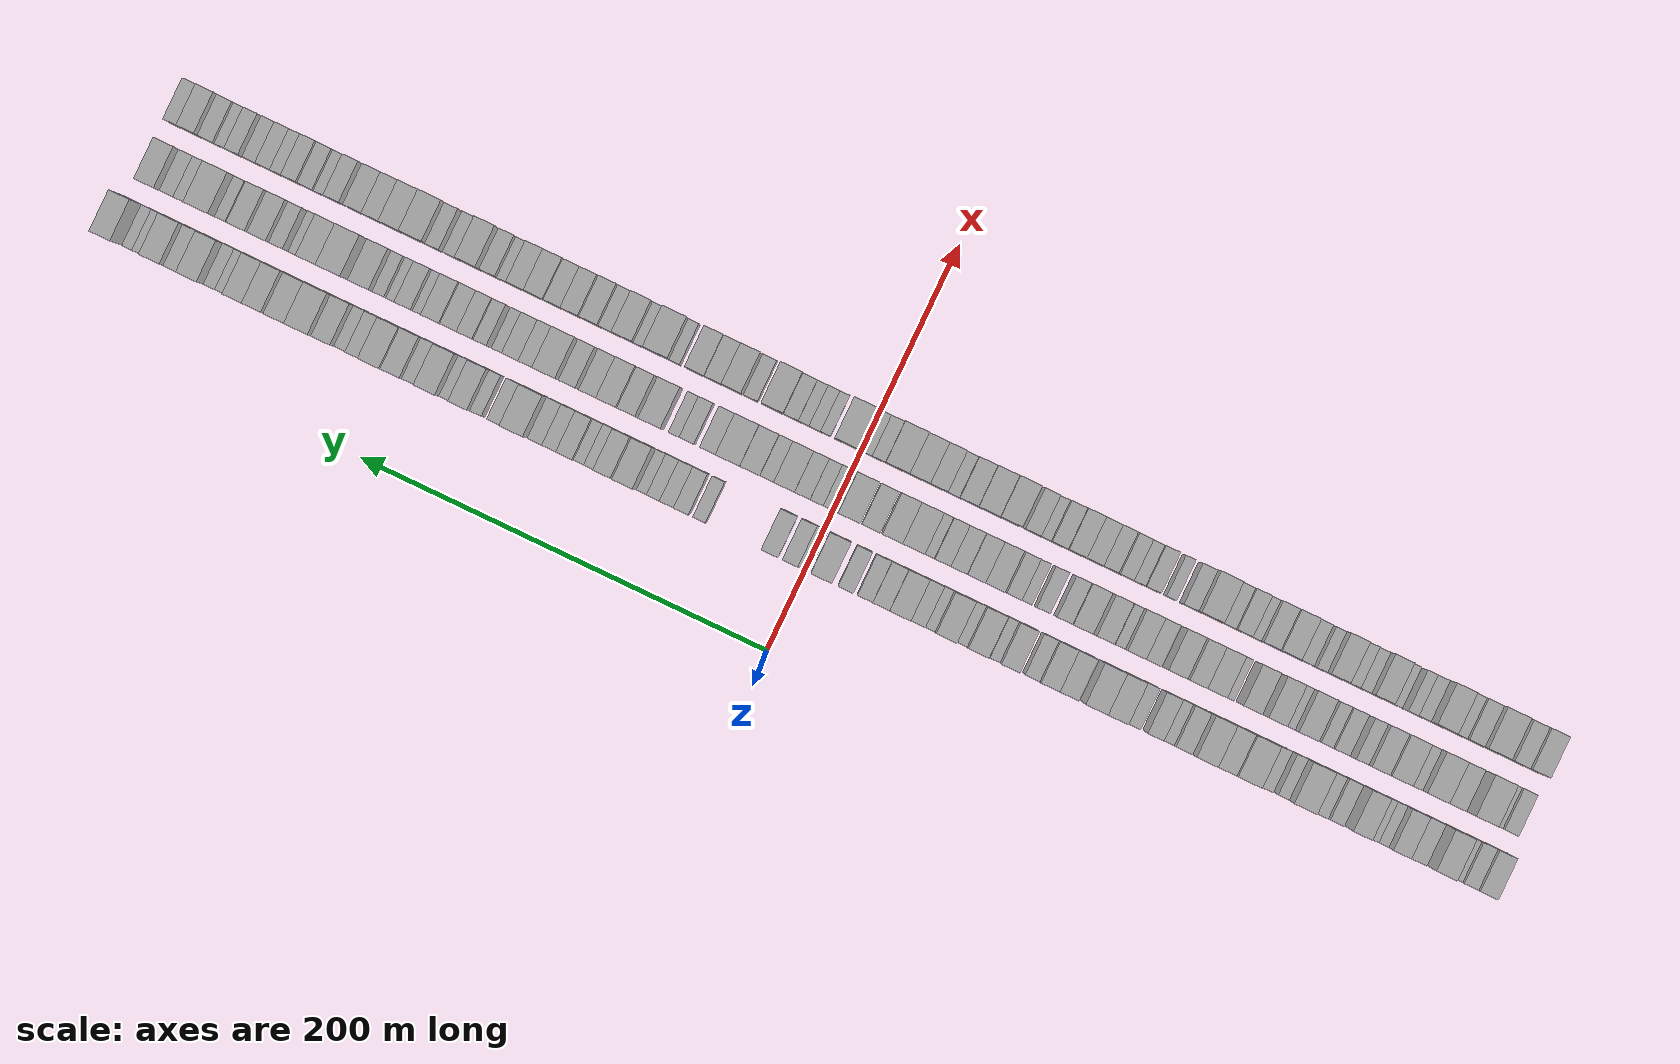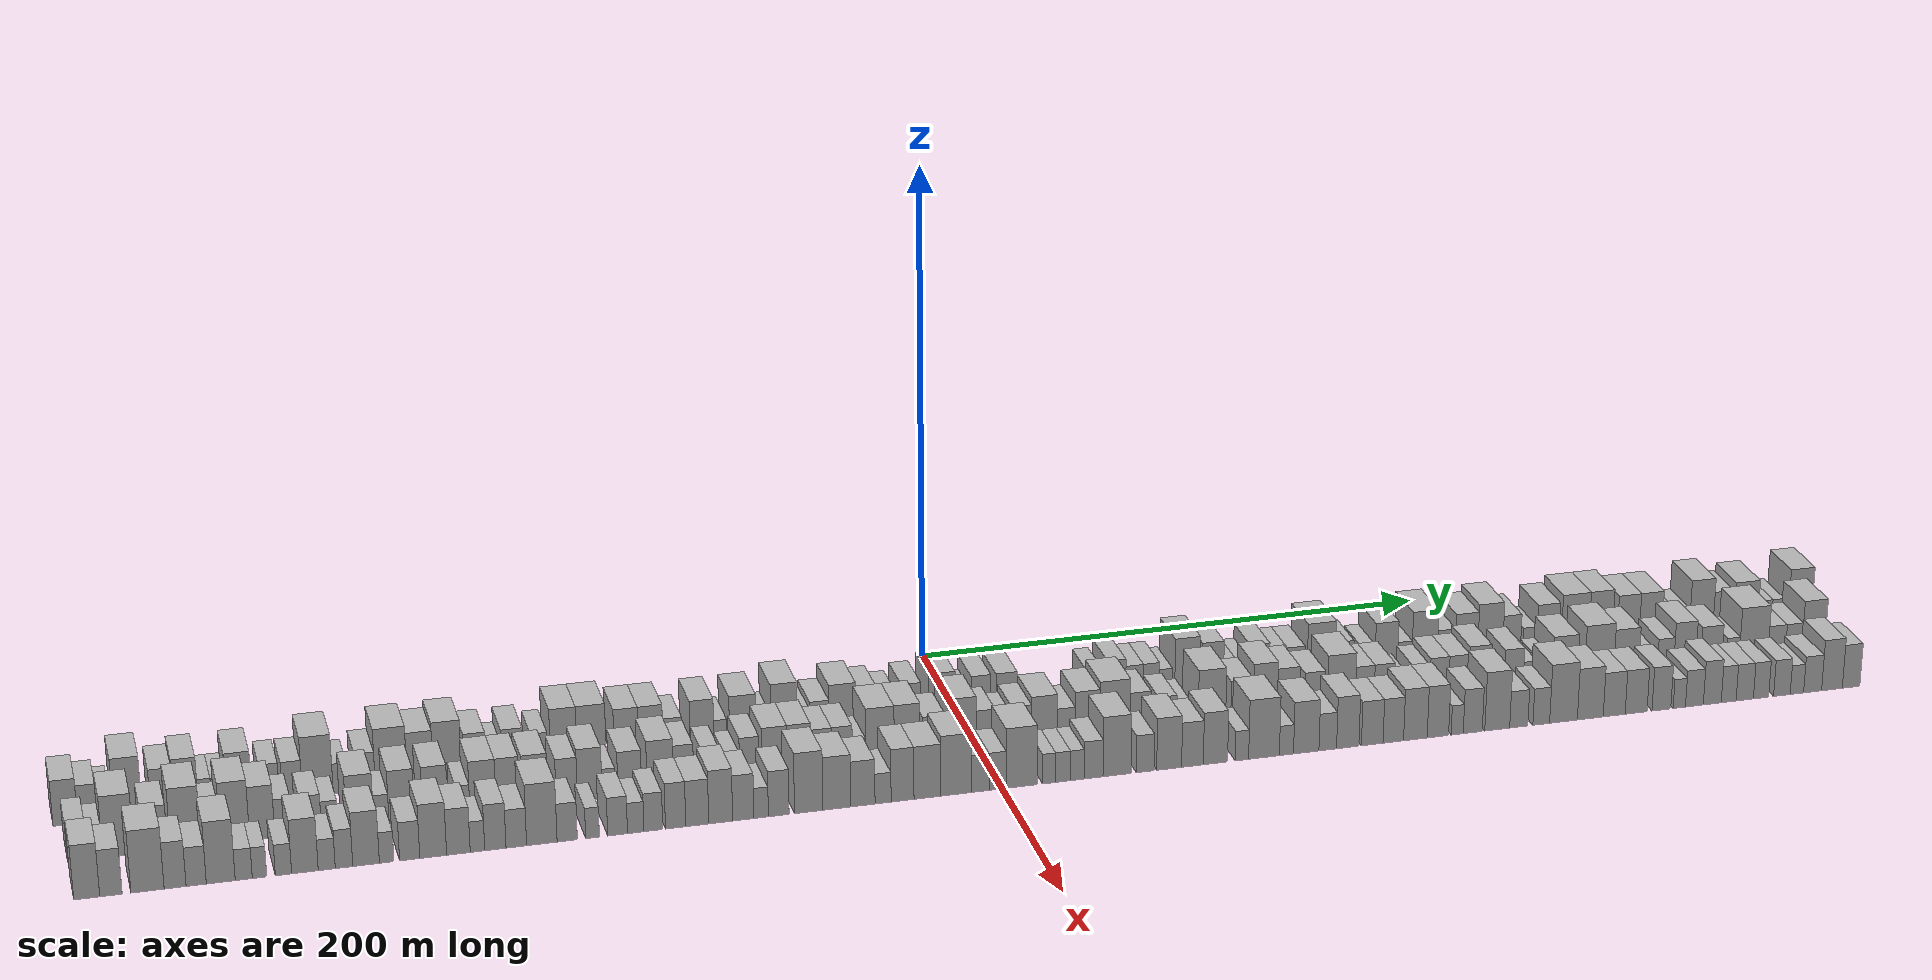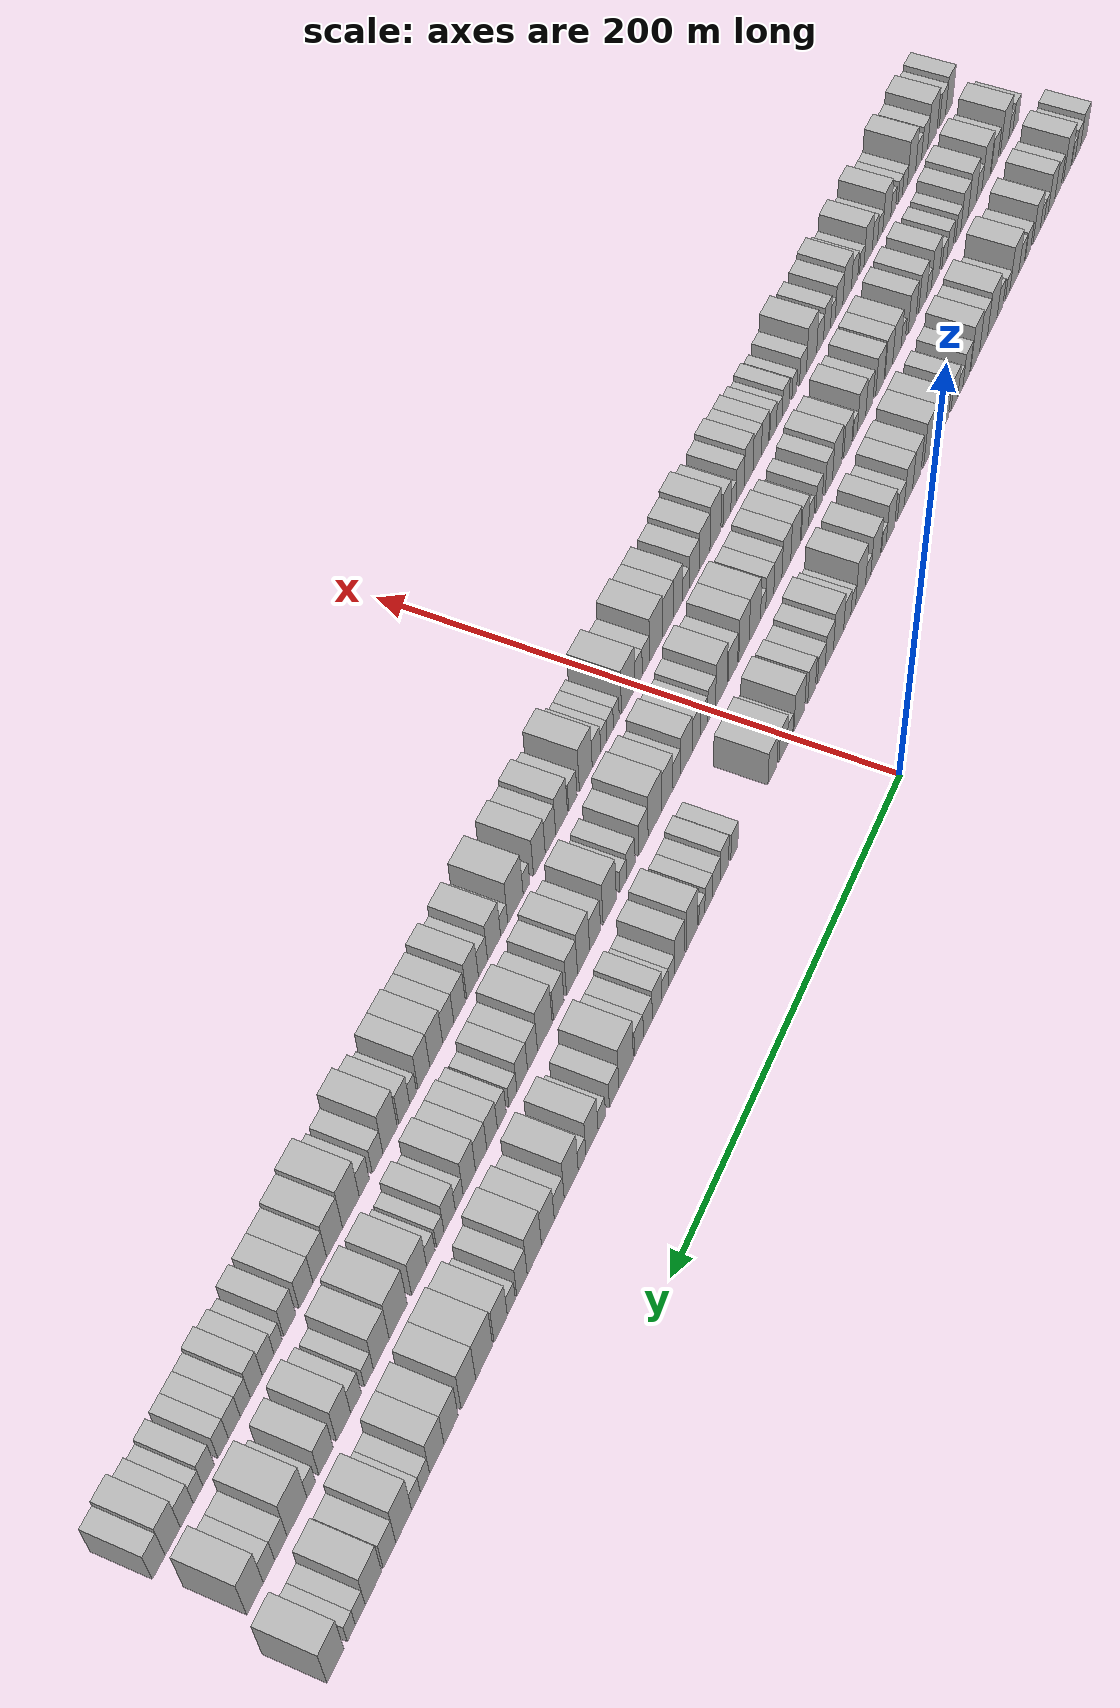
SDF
<sdf version="1.6">
 <world name="default">
  <scene>
   <sky><clouds><speed>12</speed></clouds></sky>
   <ambient>0.4 0.4 0.4 1</ambient>
   <background>0.7 0.7 0.7 1</background>
   <shadows>1</shadows>
  </scene>
  <gravity>0 0 -9.8066</gravity>
  <magnetic_field>6e-06 2.3e-05 -4.2e-05</magnetic_field>
  <physics default="0" name="default_physics" type="ode">
   <ode>
    <solver>
     <type>quick</type>
     <iters>10</iters>
     <sor>1.0</sor>
     <use_dynamic_moi_rescaling>0</use_dynamic_moi_rescaling>
    </solver>
    <constraints>
     <cfm>0</cfm>
     <erp>0.2</erp>
     <contact_max_correcting_vel>100</contact_max_correcting_vel>
     <contact_surface_layer>0.001</contact_surface_layer>
    </constraints>
   </ode>
   <max_step_size>0.004</max_step_size>
   <real_time_factor>1</real_time_factor>
   <real_time_update_rate>250</real_time_update_rate>
  </physics>
  <light name="sun" type="directional">
   <pose>0 0 10 0 0 0</pose>
   <diffuse>0.8 0.8 0.8 1</diffuse>
   <specular>0.2 0.2 0.2 1</specular>
   <attenuation>
    <range>1000</range>
    <constant>0.9</constant>
    <linear>0.01</linear>
    <quadratic>0.001</quadratic>
   </attenuation>
   <direction>-0.5 0.1 -0.9</direction>
  </light>
  <model name="building_1">
   <static>1</static>
   <pose>50.0000 -331.6268 0 0.000000 0.000000 0.000000</pose>
   <link name="link">
    <pose>0 0 9.00 0 0 0</pose>
    <collision name="collision"><geometry><box><size>20.0000 8.7465 18.0000</size></box></geometry></collision>
    <visual name="visual">
     <cast_shadows>0</cast_shadows>
     <geometry><box><size>20.0000 8.7465 18.0000</size></box></geometry>
     <material>
      <script>
       <uri>model://HANNAS_wall/materials/scripts</uri>
       <uri>model://HANNAS_wall/materials/textures</uri>
       <name>vrc/HANNAS_wall</name>
      </script>
     </material>
    </visual>
   </link>
  </model>
  <model name="building_2">
   <static>1</static>
   <pose>50.0000 -323.7669 0 0.000000 0.000000 0.000000</pose>
   <link name="link">
    <pose>0 0 7.50 0 0 0</pose>
    <collision name="collision"><geometry><box><size>20.0000 6.9732 15.0000</size></box></geometry></collision>
    <visual name="visual">
     <cast_shadows>0</cast_shadows>
     <geometry><box><size>20.0000 6.9732 15.0000</size></box></geometry>
     <material>
      <script>
       <uri>model://HANNAS_wall/materials/scripts</uri>
       <uri>model://HANNAS_wall/materials/textures</uri>
       <name>vrc/HANNAS_wall</name>
      </script>
     </material>
    </visual>
   </link>
  </model>
  <model name="building_3">
   <static>1</static>
   <pose>50.0000 -317.8753 0 0.000000 0.000000 0.000000</pose>
   <link name="link">
    <pose>0 0 6.00 0 0 0</pose>
    <collision name="collision"><geometry><box><size>20.0000 4.8100 12.0000</size></box></geometry></collision>
    <visual name="visual">
     <cast_shadows>0</cast_shadows>
     <geometry><box><size>20.0000 4.8100 12.0000</size></box></geometry>
     <material>
      <script>
       <uri>model://HANNAS_wall/materials/scripts</uri>
       <uri>model://HANNAS_wall/materials/textures</uri>
       <name>vrc/HANNAS_wall</name>
      </script>
     </material>
    </visual>
   </link>
  </model>
  <model name="building_4">
   <static>1</static>
   <pose>50.0000 -309.3967 0 0.000000 0.000000 0.000000</pose>
   <link name="link">
    <pose>0 0 12.00 0 0 0</pose>
    <collision name="collision"><geometry><box><size>20.0000 10.1470 24.0000</size></box></geometry></collision>
    <visual name="visual">
     <cast_shadows>0</cast_shadows>
     <geometry><box><size>20.0000 10.1470 24.0000</size></box></geometry>
     <material>
      <script>
       <uri>model://HANNAS_wall/materials/scripts</uri>
       <uri>model://HANNAS_wall/materials/textures</uri>
       <name>vrc/HANNAS_wall</name>
      </script>
     </material>
    </visual>
   </link>
  </model>
  <model name="building_5">
   <static>1</static>
   <pose>50.0000 -297.1925 0 0.000000 0.000000 0.000000</pose>
   <link name="link">
    <pose>0 0 9.00 0 0 0</pose>
    <collision name="collision"><geometry><box><size>20.0000 8.2614 18.0000</size></box></geometry></collision>
    <visual name="visual">
     <cast_shadows>0</cast_shadows>
     <geometry><box><size>20.0000 8.2614 18.0000</size></box></geometry>
     <material>
      <script>
       <uri>model://HANNAS_wall/materials/scripts</uri>
       <uri>model://HANNAS_wall/materials/textures</uri>
       <name>vrc/HANNAS_wall</name>
      </script>
     </material>
    </visual>
   </link>
  </model>
  <model name="building_6">
   <static>1</static>
   <pose>50.0000 -288.6831 0 0.000000 0.000000 0.000000</pose>
   <link name="link">
    <pose>0 0 10.50 0 0 0</pose>
    <collision name="collision"><geometry><box><size>20.0000 8.7574 21.0000</size></box></geometry></collision>
    <visual name="visual">
     <cast_shadows>0</cast_shadows>
     <geometry><box><size>20.0000 8.7574 21.0000</size></box></geometry>
     <material>
      <script>
       <uri>model://HANNAS_wall/materials/scripts</uri>
       <uri>model://HANNAS_wall/materials/textures</uri>
       <name>vrc/HANNAS_wall</name>
      </script>
     </material>
    </visual>
   </link>
  </model>
  <model name="building_7">
   <static>1</static>
   <pose>50.0000 -281.9020 0 0.000000 0.000000 0.000000</pose>
   <link name="link">
    <pose>0 0 6.00 0 0 0</pose>
    <collision name="collision"><geometry><box><size>20.0000 4.8047 12.0000</size></box></geometry></collision>
    <visual name="visual">
     <cast_shadows>0</cast_shadows>
     <geometry><box><size>20.0000 4.8047 12.0000</size></box></geometry>
     <material>
      <script>
       <uri>model://HANNAS_wall/materials/scripts</uri>
       <uri>model://HANNAS_wall/materials/textures</uri>
       <name>vrc/HANNAS_wall</name>
      </script>
     </material>
    </visual>
   </link>
  </model>
  <model name="building_8">
   <static>1</static>
   <pose>50.0000 -276.8866 0 0.000000 0.000000 0.000000</pose>
   <link name="link">
    <pose>0 0 6.00 0 0 0</pose>
    <collision name="collision"><geometry><box><size>20.0000 5.2261 12.0000</size></box></geometry></collision>
    <visual name="visual">
     <cast_shadows>0</cast_shadows>
     <geometry><box><size>20.0000 5.2261 12.0000</size></box></geometry>
     <material>
      <script>
       <uri>model://HANNAS_wall/materials/scripts</uri>
       <uri>model://HANNAS_wall/materials/textures</uri>
       <name>vrc/HANNAS_wall</name>
      </script>
     </material>
    </visual>
   </link>
  </model>
  <model name="building_9">
   <static>1</static>
   <pose>50.0000 -269.6459 0 0.000000 0.000000 0.000000</pose>
   <link name="link">
    <pose>0 0 10.50 0 0 0</pose>
    <collision name="collision"><geometry><box><size>20.0000 9.2554 21.0000</size></box></geometry></collision>
    <visual name="visual">
     <cast_shadows>0</cast_shadows>
     <geometry><box><size>20.0000 9.2554 21.0000</size></box></geometry>
     <material>
      <script>
       <uri>model://HANNAS_wall/materials/scripts</uri>
       <uri>model://HANNAS_wall/materials/textures</uri>
       <name>vrc/HANNAS_wall</name>
      </script>
     </material>
    </visual>
   </link>
  </model>
  <model name="building_10">
   <static>1</static>
   <pose>50.0000 -258.6013 0 0.000000 0.000000 0.000000</pose>
   <link name="link">
    <pose>0 0 7.50 0 0 0</pose>
    <collision name="collision"><geometry><box><size>20.0000 6.8338 15.0000</size></box></geometry></collision>
    <visual name="visual">
     <cast_shadows>0</cast_shadows>
     <geometry><box><size>20.0000 6.8338 15.0000</size></box></geometry>
     <material>
      <script>
       <uri>model://HANNAS_wall/materials/scripts</uri>
       <uri>model://HANNAS_wall/materials/textures</uri>
       <name>vrc/HANNAS_wall</name>
      </script>
     </material>
    </visual>
   </link>
  </model>
  <model name="building_11">
   <static>1</static>
   <pose>50.0000 -250.5868 0 0.000000 0.000000 0.000000</pose>
   <link name="link">
    <pose>0 0 7.50 0 0 0</pose>
    <collision name="collision"><geometry><box><size>20.0000 7.1953 15.0000</size></box></geometry></collision>
    <visual name="visual">
     <cast_shadows>0</cast_shadows>
     <geometry><box><size>20.0000 7.1953 15.0000</size></box></geometry>
     <material>
      <script>
       <uri>model://HANNAS_wall/materials/scripts</uri>
       <uri>model://HANNAS_wall/materials/textures</uri>
       <name>vrc/HANNAS_wall</name>
      </script>
     </material>
    </visual>
   </link>
  </model>
  <model name="building_12">
   <static>1</static>
   <pose>50.0000 -241.3926 0 0.000000 0.000000 0.000000</pose>
   <link name="link">
    <pose>0 0 12.00 0 0 0</pose>
    <collision name="collision"><geometry><box><size>20.0000 11.1932 24.0000</size></box></geometry></collision>
    <visual name="visual">
     <cast_shadows>0</cast_shadows>
     <geometry><box><size>20.0000 11.1932 24.0000</size></box></geometry>
     <material>
      <script>
       <uri>model://HANNAS_wall/materials/scripts</uri>
       <uri>model://HANNAS_wall/materials/textures</uri>
       <name>vrc/HANNAS_wall</name>
      </script>
     </material>
    </visual>
   </link>
  </model>
  <model name="building_13">
   <static>1</static>
   <pose>50.0000 -233.1363 0 0.000000 0.000000 0.000000</pose>
   <link name="link">
    <pose>0 0 6.00 0 0 0</pose>
    <collision name="collision"><geometry><box><size>20.0000 5.3193 12.0000</size></box></geometry></collision>
    <visual name="visual">
     <cast_shadows>0</cast_shadows>
     <geometry><box><size>20.0000 5.3193 12.0000</size></box></geometry>
     <material>
      <script>
       <uri>model://HANNAS_wall/materials/scripts</uri>
       <uri>model://HANNAS_wall/materials/textures</uri>
       <name>vrc/HANNAS_wall</name>
      </script>
     </material>
    </visual>
   </link>
  </model>
  <model name="building_14">
   <static>1</static>
   <pose>50.0000 -223.9610 0 0.000000 0.000000 0.000000</pose>
   <link name="link">
    <pose>0 0 7.50 0 0 0</pose>
    <collision name="collision"><geometry><box><size>20.0000 7.0312 15.0000</size></box></geometry></collision>
    <visual name="visual">
     <cast_shadows>0</cast_shadows>
     <geometry><box><size>20.0000 7.0312 15.0000</size></box></geometry>
     <material>
      <script>
       <uri>model://HANNAS_wall/materials/scripts</uri>
       <uri>model://HANNAS_wall/materials/textures</uri>
       <name>vrc/HANNAS_wall</name>
      </script>
     </material>
    </visual>
   </link>
  </model>
  <model name="building_15">
   <static>1</static>
   <pose>50.0000 -214.6187 0 0.000000 0.000000 0.000000</pose>
   <link name="link">
    <pose>0 0 12.00 0 0 0</pose>
    <collision name="collision"><geometry><box><size>20.0000 11.6534 24.0000</size></box></geometry></collision>
    <visual name="visual">
     <cast_shadows>0</cast_shadows>
     <geometry><box><size>20.0000 11.6534 24.0000</size></box></geometry>
     <material>
      <script>
       <uri>model://HANNAS_wall/materials/scripts</uri>
       <uri>model://HANNAS_wall/materials/textures</uri>
       <name>vrc/HANNAS_wall</name>
      </script>
     </material>
    </visual>
   </link>
  </model>
  <model name="building_16">
   <static>1</static>
   <pose>50.0000 -204.0040 0 0.000000 0.000000 0.000000</pose>
   <link name="link">
    <pose>0 0 10.50 0 0 0</pose>
    <collision name="collision"><geometry><box><size>20.0000 9.5760 21.0000</size></box></geometry></collision>
    <visual name="visual">
     <cast_shadows>0</cast_shadows>
     <geometry><box><size>20.0000 9.5760 21.0000</size></box></geometry>
     <material>
      <script>
       <uri>model://HANNAS_wall/materials/scripts</uri>
       <uri>model://HANNAS_wall/materials/textures</uri>
       <name>vrc/HANNAS_wall</name>
      </script>
     </material>
    </visual>
   </link>
  </model>
  <model name="building_17">
   <static>1</static>
   <pose>50.0000 -194.0085 0 0.000000 0.000000 0.000000</pose>
   <link name="link">
    <pose>0 0 12.00 0 0 0</pose>
    <collision name="collision"><geometry><box><size>20.0000 10.4152 24.0000</size></box></geometry></collision>
    <visual name="visual">
     <cast_shadows>0</cast_shadows>
     <geometry><box><size>20.0000 10.4152 24.0000</size></box></geometry>
     <material>
      <script>
       <uri>model://HANNAS_wall/materials/scripts</uri>
       <uri>model://HANNAS_wall/materials/textures</uri>
       <name>vrc/HANNAS_wall</name>
      </script>
     </material>
    </visual>
   </link>
  </model>
  <model name="building_18">
   <static>1</static>
   <pose>50.0000 -183.7888 0 0.000000 0.000000 0.000000</pose>
   <link name="link">
    <pose>0 0 9.00 0 0 0</pose>
    <collision name="collision"><geometry><box><size>20.0000 8.0241 18.0000</size></box></geometry></collision>
    <visual name="visual">
     <cast_shadows>0</cast_shadows>
     <geometry><box><size>20.0000 8.0241 18.0000</size></box></geometry>
     <material>
      <script>
       <uri>model://HANNAS_wall/materials/scripts</uri>
       <uri>model://HANNAS_wall/materials/textures</uri>
       <name>vrc/HANNAS_wall</name>
      </script>
     </material>
    </visual>
   </link>
  </model>
  <model name="building_19">
   <static>1</static>
   <pose>50.0000 -176.8450 0 0.000000 0.000000 0.000000</pose>
   <link name="link">
    <pose>0 0 6.00 0 0 0</pose>
    <collision name="collision"><geometry><box><size>20.0000 5.8635 12.0000</size></box></geometry></collision>
    <visual name="visual">
     <cast_shadows>0</cast_shadows>
     <geometry><box><size>20.0000 5.8635 12.0000</size></box></geometry>
     <material>
      <script>
       <uri>model://HANNAS_wall/materials/scripts</uri>
       <uri>model://HANNAS_wall/materials/textures</uri>
       <name>vrc/HANNAS_wall</name>
      </script>
     </material>
    </visual>
   </link>
  </model>
  <model name="building_20">
   <static>1</static>
   <pose>50.0000 -169.9643 0 0.000000 0.000000 0.000000</pose>
   <link name="link">
    <pose>0 0 9.00 0 0 0</pose>
    <collision name="collision"><geometry><box><size>20.0000 7.8979 18.0000</size></box></geometry></collision>
    <visual name="visual">
     <cast_shadows>0</cast_shadows>
     <geometry><box><size>20.0000 7.8979 18.0000</size></box></geometry>
     <material>
      <script>
       <uri>model://HANNAS_wall/materials/scripts</uri>
       <uri>model://HANNAS_wall/materials/textures</uri>
       <name>vrc/HANNAS_wall</name>
      </script>
     </material>
    </visual>
   </link>
  </model>
  <model name="building_21">
   <static>1</static>
   <pose>50.0000 -159.9730 0 0.000000 0.000000 0.000000</pose>
   <link name="link">
    <pose>0 0 7.50 0 0 0</pose>
    <collision name="collision"><geometry><box><size>20.0000 6.0848 15.0000</size></box></geometry></collision>
    <visual name="visual">
     <cast_shadows>0</cast_shadows>
     <geometry><box><size>20.0000 6.0848 15.0000</size></box></geometry>
     <material>
      <script>
       <uri>model://HANNAS_wall/materials/scripts</uri>
       <uri>model://HANNAS_wall/materials/textures</uri>
       <name>vrc/HANNAS_wall</name>
      </script>
     </material>
    </visual>
   </link>
  </model>
  <model name="building_22">
   <static>1</static>
   <pose>50.0000 -151.0170 0 0.000000 0.000000 0.000000</pose>
   <link name="link">
    <pose>0 0 12.00 0 0 0</pose>
    <collision name="collision"><geometry><box><size>20.0000 9.8271 24.0000</size></box></geometry></collision>
    <visual name="visual">
     <cast_shadows>0</cast_shadows>
     <geometry><box><size>20.0000 9.8271 24.0000</size></box></geometry>
     <material>
      <script>
       <uri>model://HANNAS_wall/materials/scripts</uri>
       <uri>model://HANNAS_wall/materials/textures</uri>
       <name>vrc/HANNAS_wall</name>
      </script>
     </material>
    </visual>
   </link>
  </model>
  <model name="building_23">
   <static>1</static>
   <pose>50.0000 -140.6810 0 0.000000 0.000000 0.000000</pose>
   <link name="link">
    <pose>0 0 12.00 0 0 0</pose>
    <collision name="collision"><geometry><box><size>20.0000 10.8451 24.0000</size></box></geometry></collision>
    <visual name="visual">
     <cast_shadows>0</cast_shadows>
     <geometry><box><size>20.0000 10.8451 24.0000</size></box></geometry>
     <material>
      <script>
       <uri>model://HANNAS_wall/materials/scripts</uri>
       <uri>model://HANNAS_wall/materials/textures</uri>
       <name>vrc/HANNAS_wall</name>
      </script>
     </material>
    </visual>
   </link>
  </model>
  <model name="building_24">
   <static>1</static>
   <pose>50.0000 -127.7165 0 0.000000 0.000000 0.000000</pose>
   <link name="link">
    <pose>0 0 10.50 0 0 0</pose>
    <collision name="collision"><geometry><box><size>20.0000 9.0838 21.0000</size></box></geometry></collision>
    <visual name="visual">
     <cast_shadows>0</cast_shadows>
     <geometry><box><size>20.0000 9.0838 21.0000</size></box></geometry>
     <material>
      <script>
       <uri>model://HANNAS_wall/materials/scripts</uri>
       <uri>model://HANNAS_wall/materials/textures</uri>
       <name>vrc/HANNAS_wall</name>
      </script>
     </material>
    </visual>
   </link>
  </model>
  <model name="building_25">
   <static>1</static>
   <pose>50.0000 -118.5763 0 0.000000 0.000000 0.000000</pose>
   <link name="link">
    <pose>0 0 10.50 0 0 0</pose>
    <collision name="collision"><geometry><box><size>20.0000 9.1967 21.0000</size></box></geometry></collision>
    <visual name="visual">
     <cast_shadows>0</cast_shadows>
     <geometry><box><size>20.0000 9.1967 21.0000</size></box></geometry>
     <material>
      <script>
       <uri>model://HANNAS_wall/materials/scripts</uri>
       <uri>model://HANNAS_wall/materials/textures</uri>
       <name>vrc/HANNAS_wall</name>
      </script>
     </material>
    </visual>
   </link>
  </model>
  <model name="building_26">
   <static>1</static>
   <pose>50.0000 -110.3898 0 0.000000 0.000000 0.000000</pose>
   <link name="link">
    <pose>0 0 7.50 0 0 0</pose>
    <collision name="collision"><geometry><box><size>20.0000 7.1761 15.0000</size></box></geometry></collision>
    <visual name="visual">
     <cast_shadows>0</cast_shadows>
     <geometry><box><size>20.0000 7.1761 15.0000</size></box></geometry>
     <material>
      <script>
       <uri>model://HANNAS_wall/materials/scripts</uri>
       <uri>model://HANNAS_wall/materials/textures</uri>
       <name>vrc/HANNAS_wall</name>
      </script>
     </material>
    </visual>
   </link>
  </model>
  <model name="building_27">
   <static>1</static>
   <pose>50.0000 -99.3260 0 0.000000 0.000000 0.000000</pose>
   <link name="link">
    <pose>0 0 10.50 0 0 0</pose>
    <collision name="collision"><geometry><box><size>20.0000 8.9515 21.0000</size></box></geometry></collision>
    <visual name="visual">
     <cast_shadows>0</cast_shadows>
     <geometry><box><size>20.0000 8.9515 21.0000</size></box></geometry>
     <material>
      <script>
       <uri>model://HANNAS_wall/materials/scripts</uri>
       <uri>model://HANNAS_wall/materials/textures</uri>
       <name>vrc/HANNAS_wall</name>
      </script>
     </material>
    </visual>
   </link>
  </model>
  <model name="building_28">
   <static>1</static>
   <pose>50.0000 -92.3775 0 0.000000 0.000000 0.000000</pose>
   <link name="link">
    <pose>0 0 6.00 0 0 0</pose>
    <collision name="collision"><geometry><box><size>20.0000 4.9455 12.0000</size></box></geometry></collision>
    <visual name="visual">
     <cast_shadows>0</cast_shadows>
     <geometry><box><size>20.0000 4.9455 12.0000</size></box></geometry>
     <material>
      <script>
       <uri>model://HANNAS_wall/materials/scripts</uri>
       <uri>model://HANNAS_wall/materials/textures</uri>
       <name>vrc/HANNAS_wall</name>
      </script>
     </material>
    </visual>
   </link>
  </model>
  <model name="building_29">
   <static>1</static>
   <pose>50.0000 -83.8792 0 0.000000 0.000000 0.000000</pose>
   <link name="link">
    <pose>0 0 10.50 0 0 0</pose>
    <collision name="collision"><geometry><box><size>20.0000 10.0511 21.0000</size></box></geometry></collision>
    <visual name="visual">
     <cast_shadows>0</cast_shadows>
     <geometry><box><size>20.0000 10.0511 21.0000</size></box></geometry>
     <material>
      <script>
       <uri>model://HANNAS_wall/materials/scripts</uri>
       <uri>model://HANNAS_wall/materials/textures</uri>
       <name>vrc/HANNAS_wall</name>
      </script>
     </material>
    </visual>
   </link>
  </model>
  <model name="building_30">
   <static>1</static>
   <pose>50.0000 -76.0548 0 0.000000 0.000000 0.000000</pose>
   <link name="link">
    <pose>0 0 6.00 0 0 0</pose>
    <collision name="collision"><geometry><box><size>20.0000 5.5977 12.0000</size></box></geometry></collision>
    <visual name="visual">
     <cast_shadows>0</cast_shadows>
     <geometry><box><size>20.0000 5.5977 12.0000</size></box></geometry>
     <material>
      <script>
       <uri>model://HANNAS_wall/materials/scripts</uri>
       <uri>model://HANNAS_wall/materials/textures</uri>
       <name>vrc/HANNAS_wall</name>
      </script>
     </material>
    </visual>
   </link>
  </model>
  <model name="building_31">
   <static>1</static>
   <pose>50.0000 -68.2252 0 0.000000 0.000000 0.000000</pose>
   <link name="link">
    <pose>0 0 12.00 0 0 0</pose>
    <collision name="collision"><geometry><box><size>20.0000 10.0615 24.0000</size></box></geometry></collision>
    <visual name="visual">
     <cast_shadows>0</cast_shadows>
     <geometry><box><size>20.0000 10.0615 24.0000</size></box></geometry>
     <material>
      <script>
       <uri>model://HANNAS_wall/materials/scripts</uri>
       <uri>model://HANNAS_wall/materials/textures</uri>
       <name>vrc/HANNAS_wall</name>
      </script>
     </material>
    </visual>
   </link>
  </model>
  <model name="building_32">
   <static>1</static>
   <pose>50.0000 -60.7939 0 0.000000 0.000000 0.000000</pose>
   <link name="link">
    <pose>0 0 6.00 0 0 0</pose>
    <collision name="collision"><geometry><box><size>20.0000 4.8011 12.0000</size></box></geometry></collision>
    <visual name="visual">
     <cast_shadows>0</cast_shadows>
     <geometry><box><size>20.0000 4.8011 12.0000</size></box></geometry>
     <material>
      <script>
       <uri>model://HANNAS_wall/materials/scripts</uri>
       <uri>model://HANNAS_wall/materials/textures</uri>
       <name>vrc/HANNAS_wall</name>
      </script>
     </material>
    </visual>
   </link>
  </model>
  <model name="building_33">
   <static>1</static>
   <pose>50.0000 -54.7445 0 0.000000 0.000000 0.000000</pose>
   <link name="link">
    <pose>0 0 7.50 0 0 0</pose>
    <collision name="collision"><geometry><box><size>20.0000 7.2978 15.0000</size></box></geometry></collision>
    <visual name="visual">
     <cast_shadows>0</cast_shadows>
     <geometry><box><size>20.0000 7.2978 15.0000</size></box></geometry>
     <material>
      <script>
       <uri>model://HANNAS_wall/materials/scripts</uri>
       <uri>model://HANNAS_wall/materials/textures</uri>
       <name>vrc/HANNAS_wall</name>
      </script>
     </material>
    </visual>
   </link>
  </model>
  <model name="building_34">
   <static>1</static>
   <pose>50.0000 -45.9717 0 0.000000 0.000000 0.000000</pose>
   <link name="link">
    <pose>0 0 10.50 0 0 0</pose>
    <collision name="collision"><geometry><box><size>20.0000 10.2478 21.0000</size></box></geometry></collision>
    <visual name="visual">
     <cast_shadows>0</cast_shadows>
     <geometry><box><size>20.0000 10.2478 21.0000</size></box></geometry>
     <material>
      <script>
       <uri>model://HANNAS_wall/materials/scripts</uri>
       <uri>model://HANNAS_wall/materials/textures</uri>
       <name>vrc/HANNAS_wall</name>
      </script>
     </material>
    </visual>
   </link>
  </model>
  <model name="building_35">
   <static>1</static>
   <pose>50.0000 -36.7895 0 0.000000 0.000000 0.000000</pose>
   <link name="link">
    <pose>0 0 9.00 0 0 0</pose>
    <collision name="collision"><geometry><box><size>20.0000 8.1166 18.0000</size></box></geometry></collision>
    <visual name="visual">
     <cast_shadows>0</cast_shadows>
     <geometry><box><size>20.0000 8.1166 18.0000</size></box></geometry>
     <material>
      <script>
       <uri>model://HANNAS_wall/materials/scripts</uri>
       <uri>model://HANNAS_wall/materials/textures</uri>
       <name>vrc/HANNAS_wall</name>
      </script>
     </material>
    </visual>
   </link>
  </model>
  <model name="building_36">
   <static>1</static>
   <pose>50.0000 -29.0209 0 0.000000 0.000000 0.000000</pose>
   <link name="link">
    <pose>0 0 7.50 0 0 0</pose>
    <collision name="collision"><geometry><box><size>20.0000 7.4207 15.0000</size></box></geometry></collision>
    <visual name="visual">
     <cast_shadows>0</cast_shadows>
     <geometry><box><size>20.0000 7.4207 15.0000</size></box></geometry>
     <material>
      <script>
       <uri>model://HANNAS_wall/materials/scripts</uri>
       <uri>model://HANNAS_wall/materials/textures</uri>
       <name>vrc/HANNAS_wall</name>
      </script>
     </material>
    </visual>
   </link>
  </model>
  <model name="building_37">
   <static>1</static>
   <pose>50.0000 -19.6073 0 0.000000 0.000000 0.000000</pose>
   <link name="link">
    <pose>0 0 9.00 0 0 0</pose>
    <collision name="collision"><geometry><box><size>20.0000 7.4065 18.0000</size></box></geometry></collision>
    <visual name="visual">
     <cast_shadows>0</cast_shadows>
     <geometry><box><size>20.0000 7.4065 18.0000</size></box></geometry>
     <material>
      <script>
       <uri>model://HANNAS_wall/materials/scripts</uri>
       <uri>model://HANNAS_wall/materials/textures</uri>
       <name>vrc/HANNAS_wall</name>
      </script>
     </material>
    </visual>
   </link>
  </model>
  <model name="building_38">
   <static>1</static>
   <pose>50.0000 -7.7778 0 0.000000 0.000000 0.000000</pose>
   <link name="link">
    <pose>0 0 10.50 0 0 0</pose>
    <collision name="collision"><geometry><box><size>20.0000 10.2526 21.0000</size></box></geometry></collision>
    <visual name="visual">
     <cast_shadows>0</cast_shadows>
     <geometry><box><size>20.0000 10.2526 21.0000</size></box></geometry>
     <material>
      <script>
       <uri>model://HANNAS_wall/materials/scripts</uri>
       <uri>model://HANNAS_wall/materials/textures</uri>
       <name>vrc/HANNAS_wall</name>
      </script>
     </material>
    </visual>
   </link>
  </model>
  <model name="building_39">
   <static>1</static>
   <pose>50.0000 1.0077 0 0.000000 0.000000 0.000000</pose>
   <link name="link">
    <pose>0 0 6.00 0 0 0</pose>
    <collision name="collision"><geometry><box><size>20.0000 5.3183 12.0000</size></box></geometry></collision>
    <visual name="visual">
     <cast_shadows>0</cast_shadows>
     <geometry><box><size>20.0000 5.3183 12.0000</size></box></geometry>
     <material>
      <script>
       <uri>model://HANNAS_wall/materials/scripts</uri>
       <uri>model://HANNAS_wall/materials/textures</uri>
       <name>vrc/HANNAS_wall</name>
      </script>
     </material>
    </visual>
   </link>
  </model>
  <model name="building_40">
   <static>1</static>
   <pose>50.0000 7.4504 0 0.000000 0.000000 0.000000</pose>
   <link name="link">
    <pose>0 0 9.00 0 0 0</pose>
    <collision name="collision"><geometry><box><size>20.0000 7.5672 18.0000</size></box></geometry></collision>
    <visual name="visual">
     <cast_shadows>0</cast_shadows>
     <geometry><box><size>20.0000 7.5672 18.0000</size></box></geometry>
     <material>
      <script>
       <uri>model://HANNAS_wall/materials/scripts</uri>
       <uri>model://HANNAS_wall/materials/textures</uri>
       <name>vrc/HANNAS_wall</name>
      </script>
     </material>
    </visual>
   </link>
  </model>
  <model name="building_41">
   <static>1</static>
   <pose>50.0000 17.3543 0 0.000000 0.000000 0.000000</pose>
   <link name="link">
    <pose>0 0 9.00 0 0 0</pose>
    <collision name="collision"><geometry><box><size>20.0000 8.2406 18.0000</size></box></geometry></collision>
    <visual name="visual">
     <cast_shadows>0</cast_shadows>
     <geometry><box><size>20.0000 8.2406 18.0000</size></box></geometry>
     <material>
      <script>
       <uri>model://HANNAS_wall/materials/scripts</uri>
       <uri>model://HANNAS_wall/materials/textures</uri>
       <name>vrc/HANNAS_wall</name>
      </script>
     </material>
    </visual>
   </link>
  </model>
  <model name="building_42">
   <static>1</static>
   <pose>50.0000 51.7338 0 0.000000 0.000000 0.000000</pose>
   <link name="link">
    <pose>0 0 7.50 0 0 0</pose>
    <collision name="collision"><geometry><box><size>20.0000 6.1729 15.0000</size></box></geometry></collision>
    <visual name="visual">
     <cast_shadows>0</cast_shadows>
     <geometry><box><size>20.0000 6.1729 15.0000</size></box></geometry>
     <material>
      <script>
       <uri>model://HANNAS_wall/materials/scripts</uri>
       <uri>model://HANNAS_wall/materials/textures</uri>
       <name>vrc/HANNAS_wall</name>
      </script>
     </material>
    </visual>
   </link>
  </model>
  <model name="building_43">
   <static>1</static>
   <pose>50.0000 60.4232 0 0.000000 0.000000 0.000000</pose>
   <link name="link">
    <pose>0 0 9.00 0 0 0</pose>
    <collision name="collision"><geometry><box><size>20.0000 7.2059 18.0000</size></box></geometry></collision>
    <visual name="visual">
     <cast_shadows>0</cast_shadows>
     <geometry><box><size>20.0000 7.2059 18.0000</size></box></geometry>
     <material>
      <script>
       <uri>model://HANNAS_wall/materials/scripts</uri>
       <uri>model://HANNAS_wall/materials/textures</uri>
       <name>vrc/HANNAS_wall</name>
      </script>
     </material>
    </visual>
   </link>
  </model>
  <model name="building_44">
   <static>1</static>
   <pose>50.0000 67.5245 0 0.000000 0.000000 0.000000</pose>
   <link name="link">
    <pose>0 0 7.50 0 0 0</pose>
    <collision name="collision"><geometry><box><size>20.0000 6.9966 15.0000</size></box></geometry></collision>
    <visual name="visual">
     <cast_shadows>0</cast_shadows>
     <geometry><box><size>20.0000 6.9966 15.0000</size></box></geometry>
     <material>
      <script>
       <uri>model://HANNAS_wall/materials/scripts</uri>
       <uri>model://HANNAS_wall/materials/textures</uri>
       <name>vrc/HANNAS_wall</name>
      </script>
     </material>
    </visual>
   </link>
  </model>
  <model name="building_45">
   <static>1</static>
   <pose>50.0000 74.1940 0 0.000000 0.000000 0.000000</pose>
   <link name="link">
    <pose>0 0 7.50 0 0 0</pose>
    <collision name="collision"><geometry><box><size>20.0000 6.3425 15.0000</size></box></geometry></collision>
    <visual name="visual">
     <cast_shadows>0</cast_shadows>
     <geometry><box><size>20.0000 6.3425 15.0000</size></box></geometry>
     <material>
      <script>
       <uri>model://HANNAS_wall/materials/scripts</uri>
       <uri>model://HANNAS_wall/materials/textures</uri>
       <name>vrc/HANNAS_wall</name>
      </script>
     </material>
    </visual>
   </link>
  </model>
  <model name="building_46">
   <static>1</static>
   <pose>50.0000 79.9017 0 0.000000 0.000000 0.000000</pose>
   <link name="link">
    <pose>0 0 6.00 0 0 0</pose>
    <collision name="collision"><geometry><box><size>20.0000 5.0729 12.0000</size></box></geometry></collision>
    <visual name="visual">
     <cast_shadows>0</cast_shadows>
     <geometry><box><size>20.0000 5.0729 12.0000</size></box></geometry>
     <material>
      <script>
       <uri>model://HANNAS_wall/materials/scripts</uri>
       <uri>model://HANNAS_wall/materials/textures</uri>
       <name>vrc/HANNAS_wall</name>
      </script>
     </material>
    </visual>
   </link>
  </model>
  <model name="building_47">
   <static>1</static>
   <pose>50.0000 88.3860 0 0.000000 0.000000 0.000000</pose>
   <link name="link">
    <pose>0 0 12.00 0 0 0</pose>
    <collision name="collision"><geometry><box><size>20.0000 9.8957 24.0000</size></box></geometry></collision>
    <visual name="visual">
     <cast_shadows>0</cast_shadows>
     <geometry><box><size>20.0000 9.8957 24.0000</size></box></geometry>
     <material>
      <script>
       <uri>model://HANNAS_wall/materials/scripts</uri>
       <uri>model://HANNAS_wall/materials/textures</uri>
       <name>vrc/HANNAS_wall</name>
      </script>
     </material>
    </visual>
   </link>
  </model>
  <model name="building_48">
   <static>1</static>
   <pose>50.0000 98.5657 0 0.000000 0.000000 0.000000</pose>
   <link name="link">
    <pose>0 0 10.50 0 0 0</pose>
    <collision name="collision"><geometry><box><size>20.0000 8.4638 21.0000</size></box></geometry></collision>
    <visual name="visual">
     <cast_shadows>0</cast_shadows>
     <geometry><box><size>20.0000 8.4638 21.0000</size></box></geometry>
     <material>
      <script>
       <uri>model://HANNAS_wall/materials/scripts</uri>
       <uri>model://HANNAS_wall/materials/textures</uri>
       <name>vrc/HANNAS_wall</name>
      </script>
     </material>
    </visual>
   </link>
  </model>
  <model name="building_49">
   <static>1</static>
   <pose>50.0000 105.4845 0 0.000000 0.000000 0.000000</pose>
   <link name="link">
    <pose>0 0 6.00 0 0 0</pose>
    <collision name="collision"><geometry><box><size>20.0000 5.3737 12.0000</size></box></geometry></collision>
    <visual name="visual">
     <cast_shadows>0</cast_shadows>
     <geometry><box><size>20.0000 5.3737 12.0000</size></box></geometry>
     <material>
      <script>
       <uri>model://HANNAS_wall/materials/scripts</uri>
       <uri>model://HANNAS_wall/materials/textures</uri>
       <name>vrc/HANNAS_wall</name>
      </script>
     </material>
    </visual>
   </link>
  </model>
  <model name="building_50">
   <static>1</static>
   <pose>50.0000 110.6867 0 0.000000 0.000000 0.000000</pose>
   <link name="link">
    <pose>0 0 6.00 0 0 0</pose>
    <collision name="collision"><geometry><box><size>20.0000 5.0306 12.0000</size></box></geometry></collision>
    <visual name="visual">
     <cast_shadows>0</cast_shadows>
     <geometry><box><size>20.0000 5.0306 12.0000</size></box></geometry>
     <material>
      <script>
       <uri>model://HANNAS_wall/materials/scripts</uri>
       <uri>model://HANNAS_wall/materials/textures</uri>
       <name>vrc/HANNAS_wall</name>
      </script>
     </material>
    </visual>
   </link>
  </model>
  <model name="building_51">
   <static>1</static>
   <pose>50.0000 117.1437 0 0.000000 0.000000 0.000000</pose>
   <link name="link">
    <pose>0 0 9.00 0 0 0</pose>
    <collision name="collision"><geometry><box><size>20.0000 7.8833 18.0000</size></box></geometry></collision>
    <visual name="visual">
     <cast_shadows>0</cast_shadows>
     <geometry><box><size>20.0000 7.8833 18.0000</size></box></geometry>
     <material>
      <script>
       <uri>model://HANNAS_wall/materials/scripts</uri>
       <uri>model://HANNAS_wall/materials/textures</uri>
       <name>vrc/HANNAS_wall</name>
      </script>
     </material>
    </visual>
   </link>
  </model>
  <model name="building_52">
   <static>1</static>
   <pose>50.0000 124.6534 0 0.000000 0.000000 0.000000</pose>
   <link name="link">
    <pose>0 0 7.50 0 0 0</pose>
    <collision name="collision"><geometry><box><size>20.0000 7.1361 15.0000</size></box></geometry></collision>
    <visual name="visual">
     <cast_shadows>0</cast_shadows>
     <geometry><box><size>20.0000 7.1361 15.0000</size></box></geometry>
     <material>
      <script>
       <uri>model://HANNAS_wall/materials/scripts</uri>
       <uri>model://HANNAS_wall/materials/textures</uri>
       <name>vrc/HANNAS_wall</name>
      </script>
     </material>
    </visual>
   </link>
  </model>
  <model name="building_53">
   <static>1</static>
   <pose>50.0000 131.7565 0 0.000000 0.000000 0.000000</pose>
   <link name="link">
    <pose>0 0 7.50 0 0 0</pose>
    <collision name="collision"><geometry><box><size>20.0000 7.0702 15.0000</size></box></geometry></collision>
    <visual name="visual">
     <cast_shadows>0</cast_shadows>
     <geometry><box><size>20.0000 7.0702 15.0000</size></box></geometry>
     <material>
      <script>
       <uri>model://HANNAS_wall/materials/scripts</uri>
       <uri>model://HANNAS_wall/materials/textures</uri>
       <name>vrc/HANNAS_wall</name>
      </script>
     </material>
    </visual>
   </link>
  </model>
  <model name="building_54">
   <static>1</static>
   <pose>50.0000 142.0020 0 0.000000 0.000000 0.000000</pose>
   <link name="link">
    <pose>0 0 12.00 0 0 0</pose>
    <collision name="collision"><geometry><box><size>20.0000 11.4209 24.0000</size></box></geometry></collision>
    <visual name="visual">
     <cast_shadows>0</cast_shadows>
     <geometry><box><size>20.0000 11.4209 24.0000</size></box></geometry>
     <material>
      <script>
       <uri>model://HANNAS_wall/materials/scripts</uri>
       <uri>model://HANNAS_wall/materials/textures</uri>
       <name>vrc/HANNAS_wall</name>
      </script>
     </material>
    </visual>
   </link>
  </model>
  <model name="building_55">
   <static>1</static>
   <pose>50.0000 151.3492 0 0.000000 0.000000 0.000000</pose>
   <link name="link">
    <pose>0 0 7.50 0 0 0</pose>
    <collision name="collision"><geometry><box><size>20.0000 7.2735 15.0000</size></box></geometry></collision>
    <visual name="visual">
     <cast_shadows>0</cast_shadows>
     <geometry><box><size>20.0000 7.2735 15.0000</size></box></geometry>
     <material>
      <script>
       <uri>model://HANNAS_wall/materials/scripts</uri>
       <uri>model://HANNAS_wall/materials/textures</uri>
       <name>vrc/HANNAS_wall</name>
      </script>
     </material>
    </visual>
   </link>
  </model>
  <model name="building_56">
   <static>1</static>
   <pose>50.0000 160.8515 0 0.000000 0.000000 0.000000</pose>
   <link name="link">
    <pose>0 0 6.00 0 0 0</pose>
    <collision name="collision"><geometry><box><size>20.0000 5.7311 12.0000</size></box></geometry></collision>
    <visual name="visual">
     <cast_shadows>0</cast_shadows>
     <geometry><box><size>20.0000 5.7311 12.0000</size></box></geometry>
     <material>
      <script>
       <uri>model://HANNAS_wall/materials/scripts</uri>
       <uri>model://HANNAS_wall/materials/textures</uri>
       <name>vrc/HANNAS_wall</name>
      </script>
     </material>
    </visual>
   </link>
  </model>
  <model name="building_57">
   <static>1</static>
   <pose>50.0000 168.3172 0 0.000000 0.000000 0.000000</pose>
   <link name="link">
    <pose>0 0 10.50 0 0 0</pose>
    <collision name="collision"><geometry><box><size>20.0000 9.2005 21.0000</size></box></geometry></collision>
    <visual name="visual">
     <cast_shadows>0</cast_shadows>
     <geometry><box><size>20.0000 9.2005 21.0000</size></box></geometry>
     <material>
      <script>
       <uri>model://HANNAS_wall/materials/scripts</uri>
       <uri>model://HANNAS_wall/materials/textures</uri>
       <name>vrc/HANNAS_wall</name>
      </script>
     </material>
    </visual>
   </link>
  </model>
  <model name="building_58">
   <static>1</static>
   <pose>50.0000 175.8092 0 0.000000 0.000000 0.000000</pose>
   <link name="link">
    <pose>0 0 6.00 0 0 0</pose>
    <collision name="collision"><geometry><box><size>20.0000 5.7834 12.0000</size></box></geometry></collision>
    <visual name="visual">
     <cast_shadows>0</cast_shadows>
     <geometry><box><size>20.0000 5.7834 12.0000</size></box></geometry>
     <material>
      <script>
       <uri>model://HANNAS_wall/materials/scripts</uri>
       <uri>model://HANNAS_wall/materials/textures</uri>
       <name>vrc/HANNAS_wall</name>
      </script>
     </material>
    </visual>
   </link>
  </model>
  <model name="building_59">
   <static>1</static>
   <pose>50.0000 183.8824 0 0.000000 0.000000 0.000000</pose>
   <link name="link">
    <pose>0 0 12.00 0 0 0</pose>
    <collision name="collision"><geometry><box><size>20.0000 10.3630 24.0000</size></box></geometry></collision>
    <visual name="visual">
     <cast_shadows>0</cast_shadows>
     <geometry><box><size>20.0000 10.3630 24.0000</size></box></geometry>
     <material>
      <script>
       <uri>model://HANNAS_wall/materials/scripts</uri>
       <uri>model://HANNAS_wall/materials/textures</uri>
       <name>vrc/HANNAS_wall</name>
      </script>
     </material>
    </visual>
   </link>
  </model>
  <model name="building_60">
   <static>1</static>
   <pose>50.0000 192.7073 0 0.000000 0.000000 0.000000</pose>
   <link name="link">
    <pose>0 0 7.50 0 0 0</pose>
    <collision name="collision"><geometry><box><size>20.0000 7.2868 15.0000</size></box></geometry></collision>
    <visual name="visual">
     <cast_shadows>0</cast_shadows>
     <geometry><box><size>20.0000 7.2868 15.0000</size></box></geometry>
     <material>
      <script>
       <uri>model://HANNAS_wall/materials/scripts</uri>
       <uri>model://HANNAS_wall/materials/textures</uri>
       <name>vrc/HANNAS_wall</name>
      </script>
     </material>
    </visual>
   </link>
  </model>
  <model name="building_61">
   <static>1</static>
   <pose>50.0000 200.9932 0 0.000000 0.000000 0.000000</pose>
   <link name="link">
    <pose>0 0 10.50 0 0 0</pose>
    <collision name="collision"><geometry><box><size>20.0000 9.2849 21.0000</size></box></geometry></collision>
    <visual name="visual">
     <cast_shadows>0</cast_shadows>
     <geometry><box><size>20.0000 9.2849 21.0000</size></box></geometry>
     <material>
      <script>
       <uri>model://HANNAS_wall/materials/scripts</uri>
       <uri>model://HANNAS_wall/materials/textures</uri>
       <name>vrc/HANNAS_wall</name>
      </script>
     </material>
    </visual>
   </link>
  </model>
  <model name="building_62">
   <static>1</static>
   <pose>50.0000 210.7724 0 0.000000 0.000000 0.000000</pose>
   <link name="link">
    <pose>0 0 12.00 0 0 0</pose>
    <collision name="collision"><geometry><box><size>20.0000 10.2734 24.0000</size></box></geometry></collision>
    <visual name="visual">
     <cast_shadows>0</cast_shadows>
     <geometry><box><size>20.0000 10.2734 24.0000</size></box></geometry>
     <material>
      <script>
       <uri>model://HANNAS_wall/materials/scripts</uri>
       <uri>model://HANNAS_wall/materials/textures</uri>
       <name>vrc/HANNAS_wall</name>
      </script>
     </material>
    </visual>
   </link>
  </model>
  <model name="building_63">
   <static>1</static>
   <pose>50.0000 219.5845 0 0.000000 0.000000 0.000000</pose>
   <link name="link">
    <pose>0 0 9.00 0 0 0</pose>
    <collision name="collision"><geometry><box><size>20.0000 7.3509 18.0000</size></box></geometry></collision>
    <visual name="visual">
     <cast_shadows>0</cast_shadows>
     <geometry><box><size>20.0000 7.3509 18.0000</size></box></geometry>
     <material>
      <script>
       <uri>model://HANNAS_wall/materials/scripts</uri>
       <uri>model://HANNAS_wall/materials/textures</uri>
       <name>vrc/HANNAS_wall</name>
      </script>
     </material>
    </visual>
   </link>
  </model>
  <model name="building_64">
   <static>1</static>
   <pose>50.0000 227.0646 0 0.000000 0.000000 0.000000</pose>
   <link name="link">
    <pose>0 0 6.00 0 0 0</pose>
    <collision name="collision"><geometry><box><size>20.0000 5.6093 12.0000</size></box></geometry></collision>
    <visual name="visual">
     <cast_shadows>0</cast_shadows>
     <geometry><box><size>20.0000 5.6093 12.0000</size></box></geometry>
     <material>
      <script>
       <uri>model://HANNAS_wall/materials/scripts</uri>
       <uri>model://HANNAS_wall/materials/textures</uri>
       <name>vrc/HANNAS_wall</name>
      </script>
     </material>
    </visual>
   </link>
  </model>
  <model name="building_65">
   <static>1</static>
   <pose>50.0000 234.4562 0 0.000000 0.000000 0.000000</pose>
   <link name="link">
    <pose>0 0 10.50 0 0 0</pose>
    <collision name="collision"><geometry><box><size>20.0000 9.1740 21.0000</size></box></geometry></collision>
    <visual name="visual">
     <cast_shadows>0</cast_shadows>
     <geometry><box><size>20.0000 9.1740 21.0000</size></box></geometry>
     <material>
      <script>
       <uri>model://HANNAS_wall/materials/scripts</uri>
       <uri>model://HANNAS_wall/materials/textures</uri>
       <name>vrc/HANNAS_wall</name>
      </script>
     </material>
    </visual>
   </link>
  </model>
  <model name="building_66">
   <static>1</static>
   <pose>50.0000 245.7895 0 0.000000 0.000000 0.000000</pose>
   <link name="link">
    <pose>0 0 12.00 0 0 0</pose>
    <collision name="collision"><geometry><box><size>20.0000 11.4926 24.0000</size></box></geometry></collision>
    <visual name="visual">
     <cast_shadows>0</cast_shadows>
     <geometry><box><size>20.0000 11.4926 24.0000</size></box></geometry>
     <material>
      <script>
       <uri>model://HANNAS_wall/materials/scripts</uri>
       <uri>model://HANNAS_wall/materials/textures</uri>
       <name>vrc/HANNAS_wall</name>
      </script>
     </material>
    </visual>
   </link>
  </model>
  <model name="building_67">
   <static>1</static>
   <pose>50.0000 256.4288 0 0.000000 0.000000 0.000000</pose>
   <link name="link">
    <pose>0 0 12.00 0 0 0</pose>
    <collision name="collision"><geometry><box><size>20.0000 9.7861 24.0000</size></box></geometry></collision>
    <visual name="visual">
     <cast_shadows>0</cast_shadows>
     <geometry><box><size>20.0000 9.7861 24.0000</size></box></geometry>
     <material>
      <script>
       <uri>model://HANNAS_wall/materials/scripts</uri>
       <uri>model://HANNAS_wall/materials/textures</uri>
       <name>vrc/HANNAS_wall</name>
      </script>
     </material>
    </visual>
   </link>
  </model>
  <model name="building_68">
   <static>1</static>
   <pose>50.0000 267.9615 0 0.000000 0.000000 0.000000</pose>
   <link name="link">
    <pose>0 0 10.50 0 0 0</pose>
    <collision name="collision"><geometry><box><size>20.0000 9.2793 21.0000</size></box></geometry></collision>
    <visual name="visual">
     <cast_shadows>0</cast_shadows>
     <geometry><box><size>20.0000 9.2793 21.0000</size></box></geometry>
     <material>
      <script>
       <uri>model://HANNAS_wall/materials/scripts</uri>
       <uri>model://HANNAS_wall/materials/textures</uri>
       <name>vrc/HANNAS_wall</name>
      </script>
     </material>
    </visual>
   </link>
  </model>
  <model name="building_69">
   <static>1</static>
   <pose>50.0000 277.3104 0 0.000000 0.000000 0.000000</pose>
   <link name="link">
    <pose>0 0 10.50 0 0 0</pose>
    <collision name="collision"><geometry><box><size>20.0000 9.4185 21.0000</size></box></geometry></collision>
    <visual name="visual">
     <cast_shadows>0</cast_shadows>
     <geometry><box><size>20.0000 9.4185 21.0000</size></box></geometry>
     <material>
      <script>
       <uri>model://HANNAS_wall/materials/scripts</uri>
       <uri>model://HANNAS_wall/materials/textures</uri>
       <name>vrc/HANNAS_wall</name>
      </script>
     </material>
    </visual>
   </link>
  </model>
  <model name="building_70">
   <static>1</static>
   <pose>50.0000 285.0077 0 0.000000 0.000000 0.000000</pose>
   <link name="link">
    <pose>0 0 6.00 0 0 0</pose>
    <collision name="collision"><geometry><box><size>20.0000 5.9760 12.0000</size></box></geometry></collision>
    <visual name="visual">
     <cast_shadows>0</cast_shadows>
     <geometry><box><size>20.0000 5.9760 12.0000</size></box></geometry>
     <material>
      <script>
       <uri>model://HANNAS_wall/materials/scripts</uri>
       <uri>model://HANNAS_wall/materials/textures</uri>
       <name>vrc/HANNAS_wall</name>
      </script>
     </material>
    </visual>
   </link>
  </model>
  <model name="building_71">
   <static>1</static>
   <pose>50.0000 290.7769 0 0.000000 0.000000 0.000000</pose>
   <link name="link">
    <pose>0 0 6.00 0 0 0</pose>
    <collision name="collision"><geometry><box><size>20.0000 5.5625 12.0000</size></box></geometry></collision>
    <visual name="visual">
     <cast_shadows>0</cast_shadows>
     <geometry><box><size>20.0000 5.5625 12.0000</size></box></geometry>
     <material>
      <script>
       <uri>model://HANNAS_wall/materials/scripts</uri>
       <uri>model://HANNAS_wall/materials/textures</uri>
       <name>vrc/HANNAS_wall</name>
      </script>
     </material>
    </visual>
   </link>
  </model>
  <model name="building_72">
   <static>1</static>
   <pose>50.0000 298.5541 0 0.000000 0.000000 0.000000</pose>
   <link name="link">
    <pose>0 0 12.00 0 0 0</pose>
    <collision name="collision"><geometry><box><size>20.0000 9.9918 24.0000</size></box></geometry></collision>
    <visual name="visual">
     <cast_shadows>0</cast_shadows>
     <geometry><box><size>20.0000 9.9918 24.0000</size></box></geometry>
     <material>
      <script>
       <uri>model://HANNAS_wall/materials/scripts</uri>
       <uri>model://HANNAS_wall/materials/textures</uri>
       <name>vrc/HANNAS_wall</name>
      </script>
     </material>
    </visual>
   </link>
  </model>
  <model name="building_73">
   <static>1</static>
   <pose>50.0000 307.4494 0 0.000000 0.000000 0.000000</pose>
   <link name="link">
    <pose>0 0 9.00 0 0 0</pose>
    <collision name="collision"><geometry><box><size>20.0000 7.7990 18.0000</size></box></geometry></collision>
    <visual name="visual">
     <cast_shadows>0</cast_shadows>
     <geometry><box><size>20.0000 7.7990 18.0000</size></box></geometry>
     <material>
      <script>
       <uri>model://HANNAS_wall/materials/scripts</uri>
       <uri>model://HANNAS_wall/materials/textures</uri>
       <name>vrc/HANNAS_wall</name>
      </script>
     </material>
    </visual>
   </link>
  </model>
  <model name="building_74">
   <static>1</static>
   <pose>50.0000 317.3789 0 0.000000 0.000000 0.000000</pose>
   <link name="link">
    <pose>0 0 10.50 0 0 0</pose>
    <collision name="collision"><geometry><box><size>20.0000 10.0600 21.0000</size></box></geometry></collision>
    <visual name="visual">
     <cast_shadows>0</cast_shadows>
     <geometry><box><size>20.0000 10.0600 21.0000</size></box></geometry>
     <material>
      <script>
       <uri>model://HANNAS_wall/materials/scripts</uri>
       <uri>model://HANNAS_wall/materials/textures</uri>
       <name>vrc/HANNAS_wall</name>
      </script>
     </material>
    </visual>
   </link>
  </model>
  <model name="building_75">
   <static>1</static>
   <pose>50.0000 325.3806 0 0.000000 0.000000 0.000000</pose>
   <link name="link">
    <pose>0 0 6.00 0 0 0</pose>
    <collision name="collision"><geometry><box><size>20.0000 5.9433 12.0000</size></box></geometry></collision>
    <visual name="visual">
     <cast_shadows>0</cast_shadows>
     <geometry><box><size>20.0000 5.9433 12.0000</size></box></geometry>
     <material>
      <script>
       <uri>model://HANNAS_wall/materials/scripts</uri>
       <uri>model://HANNAS_wall/materials/textures</uri>
       <name>vrc/HANNAS_wall</name>
      </script>
     </material>
    </visual>
   </link>
  </model>
  <model name="building_76">
   <static>1</static>
   <pose>50.0000 330.7910 0 0.000000 0.000000 0.000000</pose>
   <link name="link">
    <pose>0 0 6.00 0 0 0</pose>
    <collision name="collision"><geometry><box><size>20.0000 4.8773 12.0000</size></box></geometry></collision>
    <visual name="visual">
     <cast_shadows>0</cast_shadows>
     <geometry><box><size>20.0000 4.8773 12.0000</size></box></geometry>
     <material>
      <script>
       <uri>model://HANNAS_wall/materials/scripts</uri>
       <uri>model://HANNAS_wall/materials/textures</uri>
       <name>vrc/HANNAS_wall</name>
      </script>
     </material>
    </visual>
   </link>
  </model>
  <model name="building_77">
   <static>1</static>
   <pose>50.0000 340.2651 0 0.000000 0.000000 0.000000</pose>
   <link name="link">
    <pose>0 0 12.00 0 0 0</pose>
    <collision name="collision"><geometry><box><size>20.0000 10.0709 24.0000</size></box></geometry></collision>
    <visual name="visual">
     <cast_shadows>0</cast_shadows>
     <geometry><box><size>20.0000 10.0709 24.0000</size></box></geometry>
     <material>
      <script>
       <uri>model://HANNAS_wall/materials/scripts</uri>
       <uri>model://HANNAS_wall/materials/textures</uri>
       <name>vrc/HANNAS_wall</name>
      </script>
     </material>
    </visual>
   </link>
  </model>
  <model name="building_78">
   <static>1</static>
   <pose>79.0000 -329.5668 0 0.000000 0.000000 0.000000</pose>
   <link name="link">
    <pose>0 0 7.50 0 0 0</pose>
    <collision name="collision"><geometry><box><size>20.0000 6.8664 15.0000</size></box></geometry></collision>
    <visual name="visual">
     <cast_shadows>0</cast_shadows>
     <geometry><box><size>20.0000 6.8664 15.0000</size></box></geometry>
     <material>
      <script>
       <uri>model://HANNAS_wall/materials/scripts</uri>
       <uri>model://HANNAS_wall/materials/textures</uri>
       <name>vrc/HANNAS_wall</name>
      </script>
     </material>
    </visual>
   </link>
  </model>
  <model name="building_79">
   <static>1</static>
   <pose>79.0000 -323.4280 0 0.000000 0.000000 0.000000</pose>
   <link name="link">
    <pose>0 0 6.00 0 0 0</pose>
    <collision name="collision"><geometry><box><size>20.0000 5.4112 12.0000</size></box></geometry></collision>
    <visual name="visual">
     <cast_shadows>0</cast_shadows>
     <geometry><box><size>20.0000 5.4112 12.0000</size></box></geometry>
     <material>
      <script>
       <uri>model://HANNAS_wall/materials/scripts</uri>
       <uri>model://HANNAS_wall/materials/textures</uri>
       <name>vrc/HANNAS_wall</name>
      </script>
     </material>
    </visual>
   </link>
  </model>
  <model name="building_80">
   <static>1</static>
   <pose>79.0000 -315.2434 0 0.000000 0.000000 0.000000</pose>
   <link name="link">
    <pose>0 0 12.00 0 0 0</pose>
    <collision name="collision"><geometry><box><size>20.0000 10.9579 24.0000</size></box></geometry></collision>
    <visual name="visual">
     <cast_shadows>0</cast_shadows>
     <geometry><box><size>20.0000 10.9579 24.0000</size></box></geometry>
     <material>
      <script>
       <uri>model://HANNAS_wall/materials/scripts</uri>
       <uri>model://HANNAS_wall/materials/textures</uri>
       <name>vrc/HANNAS_wall</name>
      </script>
     </material>
    </visual>
   </link>
  </model>
  <model name="building_81">
   <static>1</static>
   <pose>79.0000 -302.3818 0 0.000000 0.000000 0.000000</pose>
   <link name="link">
    <pose>0 0 9.00 0 0 0</pose>
    <collision name="collision"><geometry><box><size>20.0000 8.7654 18.0000</size></box></geometry></collision>
    <visual name="visual">
     <cast_shadows>0</cast_shadows>
     <geometry><box><size>20.0000 8.7654 18.0000</size></box></geometry>
     <material>
      <script>
       <uri>model://HANNAS_wall/materials/scripts</uri>
       <uri>model://HANNAS_wall/materials/textures</uri>
       <name>vrc/HANNAS_wall</name>
      </script>
     </material>
    </visual>
   </link>
  </model>
  <model name="building_82">
   <static>1</static>
   <pose>79.0000 -291.6506 0 0.000000 0.000000 0.000000</pose>
   <link name="link">
    <pose>0 0 12.00 0 0 0</pose>
    <collision name="collision"><geometry><box><size>20.0000 10.6968 24.0000</size></box></geometry></collision>
    <visual name="visual">
     <cast_shadows>0</cast_shadows>
     <geometry><box><size>20.0000 10.6968 24.0000</size></box></geometry>
     <material>
      <script>
       <uri>model://HANNAS_wall/materials/scripts</uri>
       <uri>model://HANNAS_wall/materials/textures</uri>
       <name>vrc/HANNAS_wall</name>
      </script>
     </material>
    </visual>
   </link>
  </model>
  <model name="building_83">
   <static>1</static>
   <pose>79.0000 -282.8575 0 0.000000 0.000000 0.000000</pose>
   <link name="link">
    <pose>0 0 7.50 0 0 0</pose>
    <collision name="collision"><geometry><box><size>20.0000 6.8894 15.0000</size></box></geometry></collision>
    <visual name="visual">
     <cast_shadows>0</cast_shadows>
     <geometry><box><size>20.0000 6.8894 15.0000</size></box></geometry>
     <material>
      <script>
       <uri>model://HANNAS_wall/materials/scripts</uri>
       <uri>model://HANNAS_wall/materials/textures</uri>
       <name>vrc/HANNAS_wall</name>
      </script>
     </material>
    </visual>
   </link>
  </model>
  <model name="building_84">
   <static>1</static>
   <pose>79.0000 -274.2752 0 0.000000 0.000000 0.000000</pose>
   <link name="link">
    <pose>0 0 12.00 0 0 0</pose>
    <collision name="collision"><geometry><box><size>20.0000 10.2752 24.0000</size></box></geometry></collision>
    <visual name="visual">
     <cast_shadows>0</cast_shadows>
     <geometry><box><size>20.0000 10.2752 24.0000</size></box></geometry>
     <material>
      <script>
       <uri>model://HANNAS_wall/materials/scripts</uri>
       <uri>model://HANNAS_wall/materials/textures</uri>
       <name>vrc/HANNAS_wall</name>
      </script>
     </material>
    </visual>
   </link>
  </model>
  <model name="building_85">
   <static>1</static>
   <pose>79.0000 -264.6732 0 0.000000 0.000000 0.000000</pose>
   <link name="link">
    <pose>0 0 10.50 0 0 0</pose>
    <collision name="collision"><geometry><box><size>20.0000 8.9286 21.0000</size></box></geometry></collision>
    <visual name="visual">
     <cast_shadows>0</cast_shadows>
     <geometry><box><size>20.0000 8.9286 21.0000</size></box></geometry>
     <material>
      <script>
       <uri>model://HANNAS_wall/materials/scripts</uri>
       <uri>model://HANNAS_wall/materials/textures</uri>
       <name>vrc/HANNAS_wall</name>
      </script>
     </material>
    </visual>
   </link>
  </model>
  <model name="building_86">
   <static>1</static>
   <pose>79.0000 -257.1080 0 0.000000 0.000000 0.000000</pose>
   <link name="link">
    <pose>0 0 7.50 0 0 0</pose>
    <collision name="collision"><geometry><box><size>20.0000 6.2018 15.0000</size></box></geometry></collision>
    <visual name="visual">
     <cast_shadows>0</cast_shadows>
     <geometry><box><size>20.0000 6.2018 15.0000</size></box></geometry>
     <material>
      <script>
       <uri>model://HANNAS_wall/materials/scripts</uri>
       <uri>model://HANNAS_wall/materials/textures</uri>
       <name>vrc/HANNAS_wall</name>
      </script>
     </material>
    </visual>
   </link>
  </model>
  <model name="building_87">
   <static>1</static>
   <pose>79.0000 -247.3240 0 0.000000 0.000000 0.000000</pose>
   <link name="link">
    <pose>0 0 7.50 0 0 0</pose>
    <collision name="collision"><geometry><box><size>20.0000 7.3662 15.0000</size></box></geometry></collision>
    <visual name="visual">
     <cast_shadows>0</cast_shadows>
     <geometry><box><size>20.0000 7.3662 15.0000</size></box></geometry>
     <material>
      <script>
       <uri>model://HANNAS_wall/materials/scripts</uri>
       <uri>model://HANNAS_wall/materials/textures</uri>
       <name>vrc/HANNAS_wall</name>
      </script>
     </material>
    </visual>
   </link>
  </model>
  <model name="building_88">
   <static>1</static>
   <pose>79.0000 -240.6710 0 0.000000 0.000000 0.000000</pose>
   <link name="link">
    <pose>0 0 6.00 0 0 0</pose>
    <collision name="collision"><geometry><box><size>20.0000 5.9400 12.0000</size></box></geometry></collision>
    <visual name="visual">
     <cast_shadows>0</cast_shadows>
     <geometry><box><size>20.0000 5.9400 12.0000</size></box></geometry>
     <material>
      <script>
       <uri>model://HANNAS_wall/materials/scripts</uri>
       <uri>model://HANNAS_wall/materials/textures</uri>
       <name>vrc/HANNAS_wall</name>
      </script>
     </material>
    </visual>
   </link>
  </model>
  <model name="building_89">
   <static>1</static>
   <pose>79.0000 -229.8145 0 0.000000 0.000000 0.000000</pose>
   <link name="link">
    <pose>0 0 10.50 0 0 0</pose>
    <collision name="collision"><geometry><box><size>20.0000 9.7729 21.0000</size></box></geometry></collision>
    <visual name="visual">
     <cast_shadows>0</cast_shadows>
     <geometry><box><size>20.0000 9.7729 21.0000</size></box></geometry>
     <material>
      <script>
       <uri>model://HANNAS_wall/materials/scripts</uri>
       <uri>model://HANNAS_wall/materials/textures</uri>
       <name>vrc/HANNAS_wall</name>
      </script>
     </material>
    </visual>
   </link>
  </model>
  <model name="building_90">
   <static>1</static>
   <pose>79.0000 -222.2005 0 0.000000 0.000000 0.000000</pose>
   <link name="link">
    <pose>0 0 6.00 0 0 0</pose>
    <collision name="collision"><geometry><box><size>20.0000 5.4551 12.0000</size></box></geometry></collision>
    <visual name="visual">
     <cast_shadows>0</cast_shadows>
     <geometry><box><size>20.0000 5.4551 12.0000</size></box></geometry>
     <material>
      <script>
       <uri>model://HANNAS_wall/materials/scripts</uri>
       <uri>model://HANNAS_wall/materials/textures</uri>
       <name>vrc/HANNAS_wall</name>
      </script>
     </material>
    </visual>
   </link>
  </model>
  <model name="building_91">
   <static>1</static>
   <pose>79.0000 -214.8779 0 0.000000 0.000000 0.000000</pose>
   <link name="link">
    <pose>0 0 10.50 0 0 0</pose>
    <collision name="collision"><geometry><box><size>20.0000 9.1901 21.0000</size></box></geometry></collision>
    <visual name="visual">
     <cast_shadows>0</cast_shadows>
     <geometry><box><size>20.0000 9.1901 21.0000</size></box></geometry>
     <material>
      <script>
       <uri>model://HANNAS_wall/materials/scripts</uri>
       <uri>model://HANNAS_wall/materials/textures</uri>
       <name>vrc/HANNAS_wall</name>
      </script>
     </material>
    </visual>
   </link>
  </model>
  <model name="building_92">
   <static>1</static>
   <pose>79.0000 -202.7307 0 0.000000 0.000000 0.000000</pose>
   <link name="link">
    <pose>0 0 10.50 0 0 0</pose>
    <collision name="collision"><geometry><box><size>20.0000 9.1043 21.0000</size></box></geometry></collision>
    <visual name="visual">
     <cast_shadows>0</cast_shadows>
     <geometry><box><size>20.0000 9.1043 21.0000</size></box></geometry>
     <material>
      <script>
       <uri>model://HANNAS_wall/materials/scripts</uri>
       <uri>model://HANNAS_wall/materials/textures</uri>
       <name>vrc/HANNAS_wall</name>
      </script>
     </material>
    </visual>
   </link>
  </model>
  <model name="building_93">
   <static>1</static>
   <pose>79.0000 -192.7432 0 0.000000 0.000000 0.000000</pose>
   <link name="link">
    <pose>0 0 6.00 0 0 0</pose>
    <collision name="collision"><geometry><box><size>20.0000 4.8708 12.0000</size></box></geometry></collision>
    <visual name="visual">
     <cast_shadows>0</cast_shadows>
     <geometry><box><size>20.0000 4.8708 12.0000</size></box></geometry>
     <material>
      <script>
       <uri>model://HANNAS_wall/materials/scripts</uri>
       <uri>model://HANNAS_wall/materials/textures</uri>
       <name>vrc/HANNAS_wall</name>
      </script>
     </material>
    </visual>
   </link>
  </model>
  <model name="building_94">
   <static>1</static>
   <pose>79.0000 -185.5527 0 0.000000 0.000000 0.000000</pose>
   <link name="link">
    <pose>0 0 10.50 0 0 0</pose>
    <collision name="collision"><geometry><box><size>20.0000 9.5102 21.0000</size></box></geometry></collision>
    <visual name="visual">
     <cast_shadows>0</cast_shadows>
     <geometry><box><size>20.0000 9.5102 21.0000</size></box></geometry>
     <material>
      <script>
       <uri>model://HANNAS_wall/materials/scripts</uri>
       <uri>model://HANNAS_wall/materials/textures</uri>
       <name>vrc/HANNAS_wall</name>
      </script>
     </material>
    </visual>
   </link>
  </model>
  <model name="building_95">
   <static>1</static>
   <pose>79.0000 -176.4970 0 0.000000 0.000000 0.000000</pose>
   <link name="link">
    <pose>0 0 10.50 0 0 0</pose>
    <collision name="collision"><geometry><box><size>20.0000 8.6012 21.0000</size></box></geometry></collision>
    <visual name="visual">
     <cast_shadows>0</cast_shadows>
     <geometry><box><size>20.0000 8.6012 21.0000</size></box></geometry>
     <material>
      <script>
       <uri>model://HANNAS_wall/materials/scripts</uri>
       <uri>model://HANNAS_wall/materials/textures</uri>
       <name>vrc/HANNAS_wall</name>
      </script>
     </material>
    </visual>
   </link>
  </model>
  <model name="building_96">
   <static>1</static>
   <pose>79.0000 -166.5685 0 0.000000 0.000000 0.000000</pose>
   <link name="link">
    <pose>0 0 10.50 0 0 0</pose>
    <collision name="collision"><geometry><box><size>20.0000 9.2557 21.0000</size></box></geometry></collision>
    <visual name="visual">
     <cast_shadows>0</cast_shadows>
     <geometry><box><size>20.0000 9.2557 21.0000</size></box></geometry>
     <material>
      <script>
       <uri>model://HANNAS_wall/materials/scripts</uri>
       <uri>model://HANNAS_wall/materials/textures</uri>
       <name>vrc/HANNAS_wall</name>
      </script>
     </material>
    </visual>
   </link>
  </model>
  <model name="building_97">
   <static>1</static>
   <pose>79.0000 -155.0542 0 0.000000 0.000000 0.000000</pose>
   <link name="link">
    <pose>0 0 9.00 0 0 0</pose>
    <collision name="collision"><geometry><box><size>20.0000 7.7730 18.0000</size></box></geometry></collision>
    <visual name="visual">
     <cast_shadows>0</cast_shadows>
     <geometry><box><size>20.0000 7.7730 18.0000</size></box></geometry>
     <material>
      <script>
       <uri>model://HANNAS_wall/materials/scripts</uri>
       <uri>model://HANNAS_wall/materials/textures</uri>
       <name>vrc/HANNAS_wall</name>
      </script>
     </material>
    </visual>
   </link>
  </model>
  <model name="building_98">
   <static>1</static>
   <pose>79.0000 -146.6459 0 0.000000 0.000000 0.000000</pose>
   <link name="link">
    <pose>0 0 10.50 0 0 0</pose>
    <collision name="collision"><geometry><box><size>20.0000 9.0435 21.0000</size></box></geometry></collision>
    <visual name="visual">
     <cast_shadows>0</cast_shadows>
     <geometry><box><size>20.0000 9.0435 21.0000</size></box></geometry>
     <material>
      <script>
       <uri>model://HANNAS_wall/materials/scripts</uri>
       <uri>model://HANNAS_wall/materials/textures</uri>
       <name>vrc/HANNAS_wall</name>
      </script>
     </material>
    </visual>
   </link>
  </model>
  <model name="building_99">
   <static>1</static>
   <pose>79.0000 -139.7184 0 0.000000 0.000000 0.000000</pose>
   <link name="link">
    <pose>0 0 6.00 0 0 0</pose>
    <collision name="collision"><geometry><box><size>20.0000 4.8115 12.0000</size></box></geometry></collision>
    <visual name="visual">
     <cast_shadows>0</cast_shadows>
     <geometry><box><size>20.0000 4.8115 12.0000</size></box></geometry>
     <material>
      <script>
       <uri>model://HANNAS_wall/materials/scripts</uri>
       <uri>model://HANNAS_wall/materials/textures</uri>
       <name>vrc/HANNAS_wall</name>
      </script>
     </material>
    </visual>
   </link>
  </model>
  <model name="building_100">
   <static>1</static>
   <pose>79.0000 -131.9504 0 0.000000 0.000000 0.000000</pose>
   <link name="link">
    <pose>0 0 9.00 0 0 0</pose>
    <collision name="collision"><geometry><box><size>20.0000 8.7246 18.0000</size></box></geometry></collision>
    <visual name="visual">
     <cast_shadows>0</cast_shadows>
     <geometry><box><size>20.0000 8.7246 18.0000</size></box></geometry>
     <material>
      <script>
       <uri>model://HANNAS_wall/materials/scripts</uri>
       <uri>model://HANNAS_wall/materials/textures</uri>
       <name>vrc/HANNAS_wall</name>
      </script>
     </material>
    </visual>
   </link>
  </model>
  <model name="building_101">
   <static>1</static>
   <pose>79.0000 -120.7301 0 0.000000 0.000000 0.000000</pose>
   <link name="link">
    <pose>0 0 10.50 0 0 0</pose>
    <collision name="collision"><geometry><box><size>20.0000 9.7162 21.0000</size></box></geometry></collision>
    <visual name="visual">
     <cast_shadows>0</cast_shadows>
     <geometry><box><size>20.0000 9.7162 21.0000</size></box></geometry>
     <material>
      <script>
       <uri>model://HANNAS_wall/materials/scripts</uri>
       <uri>model://HANNAS_wall/materials/textures</uri>
       <name>vrc/HANNAS_wall</name>
      </script>
     </material>
    </visual>
   </link>
  </model>
  <model name="building_102">
   <static>1</static>
   <pose>79.0000 -112.0959 0 0.000000 0.000000 0.000000</pose>
   <link name="link">
    <pose>0 0 9.00 0 0 0</pose>
    <collision name="collision"><geometry><box><size>20.0000 7.5521 18.0000</size></box></geometry></collision>
    <visual name="visual">
     <cast_shadows>0</cast_shadows>
     <geometry><box><size>20.0000 7.5521 18.0000</size></box></geometry>
     <material>
      <script>
       <uri>model://HANNAS_wall/materials/scripts</uri>
       <uri>model://HANNAS_wall/materials/textures</uri>
       <name>vrc/HANNAS_wall</name>
      </script>
     </material>
    </visual>
   </link>
  </model>
  <model name="building_103">
   <static>1</static>
   <pose>79.0000 -102.0207 0 0.000000 0.000000 0.000000</pose>
   <link name="link">
    <pose>0 0 7.50 0 0 0</pose>
    <collision name="collision"><geometry><box><size>20.0000 6.5983 15.0000</size></box></geometry></collision>
    <visual name="visual">
     <cast_shadows>0</cast_shadows>
     <geometry><box><size>20.0000 6.5983 15.0000</size></box></geometry>
     <material>
      <script>
       <uri>model://HANNAS_wall/materials/scripts</uri>
       <uri>model://HANNAS_wall/materials/textures</uri>
       <name>vrc/HANNAS_wall</name>
      </script>
     </material>
    </visual>
   </link>
  </model>
  <model name="building_104">
   <static>1</static>
   <pose>79.0000 -93.9938 0 0.000000 0.000000 0.000000</pose>
   <link name="link">
    <pose>0 0 6.00 0 0 0</pose>
    <collision name="collision"><geometry><box><size>20.0000 5.4555 12.0000</size></box></geometry></collision>
    <visual name="visual">
     <cast_shadows>0</cast_shadows>
     <geometry><box><size>20.0000 5.4555 12.0000</size></box></geometry>
     <material>
      <script>
       <uri>model://HANNAS_wall/materials/scripts</uri>
       <uri>model://HANNAS_wall/materials/textures</uri>
       <name>vrc/HANNAS_wall</name>
      </script>
     </material>
    </visual>
   </link>
  </model>
  <model name="building_105">
   <static>1</static>
   <pose>79.0000 -87.5949 0 0.000000 0.000000 0.000000</pose>
   <link name="link">
    <pose>0 0 9.00 0 0 0</pose>
    <collision name="collision"><geometry><box><size>20.0000 7.3423 18.0000</size></box></geometry></collision>
    <visual name="visual">
     <cast_shadows>0</cast_shadows>
     <geometry><box><size>20.0000 7.3423 18.0000</size></box></geometry>
     <material>
      <script>
       <uri>model://HANNAS_wall/materials/scripts</uri>
       <uri>model://HANNAS_wall/materials/textures</uri>
       <name>vrc/HANNAS_wall</name>
      </script>
     </material>
    </visual>
   </link>
  </model>
  <model name="building_106">
   <static>1</static>
   <pose>79.0000 -78.1845 0 0.000000 0.000000 0.000000</pose>
   <link name="link">
    <pose>0 0 10.50 0 0 0</pose>
    <collision name="collision"><geometry><box><size>20.0000 9.4783 21.0000</size></box></geometry></collision>
    <visual name="visual">
     <cast_shadows>0</cast_shadows>
     <geometry><box><size>20.0000 9.4783 21.0000</size></box></geometry>
     <material>
      <script>
       <uri>model://HANNAS_wall/materials/scripts</uri>
       <uri>model://HANNAS_wall/materials/textures</uri>
       <name>vrc/HANNAS_wall</name>
      </script>
     </material>
    </visual>
   </link>
  </model>
  <model name="building_107">
   <static>1</static>
   <pose>79.0000 -69.0837 0 0.000000 0.000000 0.000000</pose>
   <link name="link">
    <pose>0 0 10.50 0 0 0</pose>
    <collision name="collision"><geometry><box><size>20.0000 8.7234 21.0000</size></box></geometry></collision>
    <visual name="visual">
     <cast_shadows>0</cast_shadows>
     <geometry><box><size>20.0000 8.7234 21.0000</size></box></geometry>
     <material>
      <script>
       <uri>model://HANNAS_wall/materials/scripts</uri>
       <uri>model://HANNAS_wall/materials/textures</uri>
       <name>vrc/HANNAS_wall</name>
      </script>
     </material>
    </visual>
   </link>
  </model>
  <model name="building_108">
   <static>1</static>
   <pose>79.0000 -60.7558 0 0.000000 0.000000 0.000000</pose>
   <link name="link">
    <pose>0 0 9.00 0 0 0</pose>
    <collision name="collision"><geometry><box><size>20.0000 7.9325 18.0000</size></box></geometry></collision>
    <visual name="visual">
     <cast_shadows>0</cast_shadows>
     <geometry><box><size>20.0000 7.9325 18.0000</size></box></geometry>
     <material>
      <script>
       <uri>model://HANNAS_wall/materials/scripts</uri>
       <uri>model://HANNAS_wall/materials/textures</uri>
       <name>vrc/HANNAS_wall</name>
      </script>
     </material>
    </visual>
   </link>
  </model>
  <model name="building_109">
   <static>1</static>
   <pose>79.0000 -52.9318 0 0.000000 0.000000 0.000000</pose>
   <link name="link">
    <pose>0 0 9.00 0 0 0</pose>
    <collision name="collision"><geometry><box><size>20.0000 7.7155 18.0000</size></box></geometry></collision>
    <visual name="visual">
     <cast_shadows>0</cast_shadows>
     <geometry><box><size>20.0000 7.7155 18.0000</size></box></geometry>
     <material>
      <script>
       <uri>model://HANNAS_wall/materials/scripts</uri>
       <uri>model://HANNAS_wall/materials/textures</uri>
       <name>vrc/HANNAS_wall</name>
      </script>
     </material>
    </visual>
   </link>
  </model>
  <model name="building_110">
   <static>1</static>
   <pose>79.0000 -46.5285 0 0.000000 0.000000 0.000000</pose>
   <link name="link">
    <pose>0 0 6.00 0 0 0</pose>
    <collision name="collision"><geometry><box><size>20.0000 5.0912 12.0000</size></box></geometry></collision>
    <visual name="visual">
     <cast_shadows>0</cast_shadows>
     <geometry><box><size>20.0000 5.0912 12.0000</size></box></geometry>
     <material>
      <script>
       <uri>model://HANNAS_wall/materials/scripts</uri>
       <uri>model://HANNAS_wall/materials/textures</uri>
       <name>vrc/HANNAS_wall</name>
      </script>
     </material>
    </visual>
   </link>
  </model>
  <model name="building_111">
   <static>1</static>
   <pose>79.0000 -38.6144 0 0.000000 0.000000 0.000000</pose>
   <link name="link">
    <pose>0 0 12.00 0 0 0</pose>
    <collision name="collision"><geometry><box><size>20.0000 10.7369 24.0000</size></box></geometry></collision>
    <visual name="visual">
     <cast_shadows>0</cast_shadows>
     <geometry><box><size>20.0000 10.7369 24.0000</size></box></geometry>
     <material>
      <script>
       <uri>model://HANNAS_wall/materials/scripts</uri>
       <uri>model://HANNAS_wall/materials/textures</uri>
       <name>vrc/HANNAS_wall</name>
      </script>
     </material>
    </visual>
   </link>
  </model>
  <model name="building_112">
   <static>1</static>
   <pose>79.0000 -28.3461 0 0.000000 0.000000 0.000000</pose>
   <link name="link">
    <pose>0 0 12.00 0 0 0</pose>
    <collision name="collision"><geometry><box><size>20.0000 9.7996 24.0000</size></box></geometry></collision>
    <visual name="visual">
     <cast_shadows>0</cast_shadows>
     <geometry><box><size>20.0000 9.7996 24.0000</size></box></geometry>
     <material>
      <script>
       <uri>model://HANNAS_wall/materials/scripts</uri>
       <uri>model://HANNAS_wall/materials/textures</uri>
       <name>vrc/HANNAS_wall</name>
      </script>
     </material>
    </visual>
   </link>
  </model>
  <model name="building_113">
   <static>1</static>
   <pose>79.0000 -18.0942 0 0.000000 0.000000 0.000000</pose>
   <link name="link">
    <pose>0 0 9.00 0 0 0</pose>
    <collision name="collision"><geometry><box><size>20.0000 8.7042 18.0000</size></box></geometry></collision>
    <visual name="visual">
     <cast_shadows>0</cast_shadows>
     <geometry><box><size>20.0000 8.7042 18.0000</size></box></geometry>
     <material>
      <script>
       <uri>model://HANNAS_wall/materials/scripts</uri>
       <uri>model://HANNAS_wall/materials/textures</uri>
       <name>vrc/HANNAS_wall</name>
      </script>
     </material>
    </visual>
   </link>
  </model>
  <model name="building_114">
   <static>1</static>
   <pose>79.0000 -7.4302 0 0.000000 0.000000 0.000000</pose>
   <link name="link">
    <pose>0 0 12.00 0 0 0</pose>
    <collision name="collision"><geometry><box><size>20.0000 10.6237 24.0000</size></box></geometry></collision>
    <visual name="visual">
     <cast_shadows>0</cast_shadows>
     <geometry><box><size>20.0000 10.6237 24.0000</size></box></geometry>
     <material>
      <script>
       <uri>model://HANNAS_wall/materials/scripts</uri>
       <uri>model://HANNAS_wall/materials/textures</uri>
       <name>vrc/HANNAS_wall</name>
      </script>
     </material>
    </visual>
   </link>
  </model>
  <model name="building_115">
   <static>1</static>
   <pose>79.0000 1.4939 0 0.000000 0.000000 0.000000</pose>
   <link name="link">
    <pose>0 0 9.00 0 0 0</pose>
    <collision name="collision"><geometry><box><size>20.0000 7.2247 18.0000</size></box></geometry></collision>
    <visual name="visual">
     <cast_shadows>0</cast_shadows>
     <geometry><box><size>20.0000 7.2247 18.0000</size></box></geometry>
     <material>
      <script>
       <uri>model://HANNAS_wall/materials/scripts</uri>
       <uri>model://HANNAS_wall/materials/textures</uri>
       <name>vrc/HANNAS_wall</name>
      </script>
     </material>
    </visual>
   </link>
  </model>
  <model name="building_116">
   <static>1</static>
   <pose>79.0000 8.2973 0 0.000000 0.000000 0.000000</pose>
   <link name="link">
    <pose>0 0 7.50 0 0 0</pose>
    <collision name="collision"><geometry><box><size>20.0000 6.3820 15.0000</size></box></geometry></collision>
    <visual name="visual">
     <cast_shadows>0</cast_shadows>
     <geometry><box><size>20.0000 6.3820 15.0000</size></box></geometry>
     <material>
      <script>
       <uri>model://HANNAS_wall/materials/scripts</uri>
       <uri>model://HANNAS_wall/materials/textures</uri>
       <name>vrc/HANNAS_wall</name>
      </script>
     </material>
    </visual>
   </link>
  </model>
  <model name="building_117">
   <static>1</static>
   <pose>79.0000 15.2672 0 0.000000 0.000000 0.000000</pose>
   <link name="link">
    <pose>0 0 9.00 0 0 0</pose>
    <collision name="collision"><geometry><box><size>20.0000 7.5578 18.0000</size></box></geometry></collision>
    <visual name="visual">
     <cast_shadows>0</cast_shadows>
     <geometry><box><size>20.0000 7.5578 18.0000</size></box></geometry>
     <material>
      <script>
       <uri>model://HANNAS_wall/materials/scripts</uri>
       <uri>model://HANNAS_wall/materials/textures</uri>
       <name>vrc/HANNAS_wall</name>
      </script>
     </material>
    </visual>
   </link>
  </model>
  <model name="building_118">
   <static>1</static>
   <pose>79.0000 24.0853 0 0.000000 0.000000 0.000000</pose>
   <link name="link">
    <pose>0 0 10.50 0 0 0</pose>
    <collision name="collision"><geometry><box><size>20.0000 10.0784 21.0000</size></box></geometry></collision>
    <visual name="visual">
     <cast_shadows>0</cast_shadows>
     <geometry><box><size>20.0000 10.0784 21.0000</size></box></geometry>
     <material>
      <script>
       <uri>model://HANNAS_wall/materials/scripts</uri>
       <uri>model://HANNAS_wall/materials/textures</uri>
       <name>vrc/HANNAS_wall</name>
      </script>
     </material>
    </visual>
   </link>
  </model>
  <model name="building_119">
   <static>1</static>
   <pose>79.0000 32.4928 0 0.000000 0.000000 0.000000</pose>
   <link name="link">
    <pose>0 0 7.50 0 0 0</pose>
    <collision name="collision"><geometry><box><size>20.0000 6.7366 15.0000</size></box></geometry></collision>
    <visual name="visual">
     <cast_shadows>0</cast_shadows>
     <geometry><box><size>20.0000 6.7366 15.0000</size></box></geometry>
     <material>
      <script>
       <uri>model://HANNAS_wall/materials/scripts</uri>
       <uri>model://HANNAS_wall/materials/textures</uri>
       <name>vrc/HANNAS_wall</name>
      </script>
     </material>
    </visual>
   </link>
  </model>
  <model name="building_120">
   <static>1</static>
   <pose>79.0000 40.6600 0 0.000000 0.000000 0.000000</pose>
   <link name="link">
    <pose>0 0 10.50 0 0 0</pose>
    <collision name="collision"><geometry><box><size>20.0000 9.5979 21.0000</size></box></geometry></collision>
    <visual name="visual">
     <cast_shadows>0</cast_shadows>
     <geometry><box><size>20.0000 9.5979 21.0000</size></box></geometry>
     <material>
      <script>
       <uri>model://HANNAS_wall/materials/scripts</uri>
       <uri>model://HANNAS_wall/materials/textures</uri>
       <name>vrc/HANNAS_wall</name>
      </script>
     </material>
    </visual>
   </link>
  </model>
  <model name="building_121">
   <static>1</static>
   <pose>79.0000 51.3316 0 0.000000 0.000000 0.000000</pose>
   <link name="link">
    <pose>0 0 12.00 0 0 0</pose>
    <collision name="collision"><geometry><box><size>20.0000 11.7453 24.0000</size></box></geometry></collision>
    <visual name="visual">
     <cast_shadows>0</cast_shadows>
     <geometry><box><size>20.0000 11.7453 24.0000</size></box></geometry>
     <material>
      <script>
       <uri>model://HANNAS_wall/materials/scripts</uri>
       <uri>model://HANNAS_wall/materials/textures</uri>
       <name>vrc/HANNAS_wall</name>
      </script>
     </material>
    </visual>
   </link>
  </model>
  <model name="building_122">
   <static>1</static>
   <pose>79.0000 61.1609 0 0.000000 0.000000 0.000000</pose>
   <link name="link">
    <pose>0 0 9.00 0 0 0</pose>
    <collision name="collision"><geometry><box><size>20.0000 7.9132 18.0000</size></box></geometry></collision>
    <visual name="visual">
     <cast_shadows>0</cast_shadows>
     <geometry><box><size>20.0000 7.9132 18.0000</size></box></geometry>
     <material>
      <script>
       <uri>model://HANNAS_wall/materials/scripts</uri>
       <uri>model://HANNAS_wall/materials/textures</uri>
       <name>vrc/HANNAS_wall</name>
      </script>
     </material>
    </visual>
   </link>
  </model>
  <model name="building_123">
   <static>1</static>
   <pose>79.0000 71.6777 0 0.000000 0.000000 0.000000</pose>
   <link name="link">
    <pose>0 0 7.50 0 0 0</pose>
    <collision name="collision"><geometry><box><size>20.0000 7.1204 15.0000</size></box></geometry></collision>
    <visual name="visual">
     <cast_shadows>0</cast_shadows>
     <geometry><box><size>20.0000 7.1204 15.0000</size></box></geometry>
     <material>
      <script>
       <uri>model://HANNAS_wall/materials/scripts</uri>
       <uri>model://HANNAS_wall/materials/textures</uri>
       <name>vrc/HANNAS_wall</name>
      </script>
     </material>
    </visual>
   </link>
  </model>
  <model name="building_124">
   <static>1</static>
   <pose>79.0000 77.9677 0 0.000000 0.000000 0.000000</pose>
   <link name="link">
    <pose>0 0 6.00 0 0 0</pose>
    <collision name="collision"><geometry><box><size>20.0000 5.4597 12.0000</size></box></geometry></collision>
    <visual name="visual">
     <cast_shadows>0</cast_shadows>
     <geometry><box><size>20.0000 5.4597 12.0000</size></box></geometry>
     <material>
      <script>
       <uri>model://HANNAS_wall/materials/scripts</uri>
       <uri>model://HANNAS_wall/materials/textures</uri>
       <name>vrc/HANNAS_wall</name>
      </script>
     </material>
    </visual>
   </link>
  </model>
  <model name="building_125">
   <static>1</static>
   <pose>79.0000 89.0785 0 0.000000 0.000000 0.000000</pose>
   <link name="link">
    <pose>0 0 12.00 0 0 0</pose>
    <collision name="collision"><geometry><box><size>20.0000 10.7621 24.0000</size></box></geometry></collision>
    <visual name="visual">
     <cast_shadows>0</cast_shadows>
     <geometry><box><size>20.0000 10.7621 24.0000</size></box></geometry>
     <material>
      <script>
       <uri>model://HANNAS_wall/materials/scripts</uri>
       <uri>model://HANNAS_wall/materials/textures</uri>
       <name>vrc/HANNAS_wall</name>
      </script>
     </material>
    </visual>
   </link>
  </model>
  <model name="building_126">
   <static>1</static>
   <pose>79.0000 100.8527 0 0.000000 0.000000 0.000000</pose>
   <link name="link">
    <pose>0 0 9.00 0 0 0</pose>
    <collision name="collision"><geometry><box><size>20.0000 8.7864 18.0000</size></box></geometry></collision>
    <visual name="visual">
     <cast_shadows>0</cast_shadows>
     <geometry><box><size>20.0000 8.7864 18.0000</size></box></geometry>
     <material>
      <script>
       <uri>model://HANNAS_wall/materials/scripts</uri>
       <uri>model://HANNAS_wall/materials/textures</uri>
       <name>vrc/HANNAS_wall</name>
      </script>
     </material>
    </visual>
   </link>
  </model>
  <model name="building_127">
   <static>1</static>
   <pose>79.0000 110.0501 0 0.000000 0.000000 0.000000</pose>
   <link name="link">
    <pose>0 0 12.00 0 0 0</pose>
    <collision name="collision"><geometry><box><size>20.0000 9.6083 24.0000</size></box></geometry></collision>
    <visual name="visual">
     <cast_shadows>0</cast_shadows>
     <geometry><box><size>20.0000 9.6083 24.0000</size></box></geometry>
     <material>
      <script>
       <uri>model://HANNAS_wall/materials/scripts</uri>
       <uri>model://HANNAS_wall/materials/textures</uri>
       <name>vrc/HANNAS_wall</name>
      </script>
     </material>
    </visual>
   </link>
  </model>
  <model name="building_128">
   <static>1</static>
   <pose>79.0000 119.1418 0 0.000000 0.000000 0.000000</pose>
   <link name="link">
    <pose>0 0 10.50 0 0 0</pose>
    <collision name="collision"><geometry><box><size>20.0000 8.5752 21.0000</size></box></geometry></collision>
    <visual name="visual">
     <cast_shadows>0</cast_shadows>
     <geometry><box><size>20.0000 8.5752 21.0000</size></box></geometry>
     <material>
      <script>
       <uri>model://HANNAS_wall/materials/scripts</uri>
       <uri>model://HANNAS_wall/materials/textures</uri>
       <name>vrc/HANNAS_wall</name>
      </script>
     </material>
    </visual>
   </link>
  </model>
  <model name="building_129">
   <static>1</static>
   <pose>79.0000 129.4755 0 0.000000 0.000000 0.000000</pose>
   <link name="link">
    <pose>0 0 9.00 0 0 0</pose>
    <collision name="collision"><geometry><box><size>20.0000 8.0923 18.0000</size></box></geometry></collision>
    <visual name="visual">
     <cast_shadows>0</cast_shadows>
     <geometry><box><size>20.0000 8.0923 18.0000</size></box></geometry>
     <material>
      <script>
       <uri>model://HANNAS_wall/materials/scripts</uri>
       <uri>model://HANNAS_wall/materials/textures</uri>
       <name>vrc/HANNAS_wall</name>
      </script>
     </material>
    </visual>
   </link>
  </model>
  <model name="building_130">
   <static>1</static>
   <pose>79.0000 140.1061 0 0.000000 0.000000 0.000000</pose>
   <link name="link">
    <pose>0 0 12.00 0 0 0</pose>
    <collision name="collision"><geometry><box><size>20.0000 11.1688 24.0000</size></box></geometry></collision>
    <visual name="visual">
     <cast_shadows>0</cast_shadows>
     <geometry><box><size>20.0000 11.1688 24.0000</size></box></geometry>
     <material>
      <script>
       <uri>model://HANNAS_wall/materials/scripts</uri>
       <uri>model://HANNAS_wall/materials/textures</uri>
       <name>vrc/HANNAS_wall</name>
      </script>
     </material>
    </visual>
   </link>
  </model>
  <model name="building_131">
   <static>1</static>
   <pose>79.0000 149.4155 0 0.000000 0.000000 0.000000</pose>
   <link name="link">
    <pose>0 0 9.00 0 0 0</pose>
    <collision name="collision"><geometry><box><size>20.0000 7.4500 18.0000</size></box></geometry></collision>
    <visual name="visual">
     <cast_shadows>0</cast_shadows>
     <geometry><box><size>20.0000 7.4500 18.0000</size></box></geometry>
     <material>
      <script>
       <uri>model://HANNAS_wall/materials/scripts</uri>
       <uri>model://HANNAS_wall/materials/textures</uri>
       <name>vrc/HANNAS_wall</name>
      </script>
     </material>
    </visual>
   </link>
  </model>
  <model name="building_132">
   <static>1</static>
   <pose>79.0000 157.1162 0 0.000000 0.000000 0.000000</pose>
   <link name="link">
    <pose>0 0 9.00 0 0 0</pose>
    <collision name="collision"><geometry><box><size>20.0000 7.9513 18.0000</size></box></geometry></collision>
    <visual name="visual">
     <cast_shadows>0</cast_shadows>
     <geometry><box><size>20.0000 7.9513 18.0000</size></box></geometry>
     <material>
      <script>
       <uri>model://HANNAS_wall/materials/scripts</uri>
       <uri>model://HANNAS_wall/materials/textures</uri>
       <name>vrc/HANNAS_wall</name>
      </script>
     </material>
    </visual>
   </link>
  </model>
  <model name="building_133">
   <static>1</static>
   <pose>79.0000 164.0269 0 0.000000 0.000000 0.000000</pose>
   <link name="link">
    <pose>0 0 6.00 0 0 0</pose>
    <collision name="collision"><geometry><box><size>20.0000 5.8700 12.0000</size></box></geometry></collision>
    <visual name="visual">
     <cast_shadows>0</cast_shadows>
     <geometry><box><size>20.0000 5.8700 12.0000</size></box></geometry>
     <material>
      <script>
       <uri>model://HANNAS_wall/materials/scripts</uri>
       <uri>model://HANNAS_wall/materials/textures</uri>
       <name>vrc/HANNAS_wall</name>
      </script>
     </material>
    </visual>
   </link>
  </model>
  <model name="building_134">
   <static>1</static>
   <pose>79.0000 172.1776 0 0.000000 0.000000 0.000000</pose>
   <link name="link">
    <pose>0 0 7.50 0 0 0</pose>
    <collision name="collision"><geometry><box><size>20.0000 6.4314 15.0000</size></box></geometry></collision>
    <visual name="visual">
     <cast_shadows>0</cast_shadows>
     <geometry><box><size>20.0000 6.4314 15.0000</size></box></geometry>
     <material>
      <script>
       <uri>model://HANNAS_wall/materials/scripts</uri>
       <uri>model://HANNAS_wall/materials/textures</uri>
       <name>vrc/HANNAS_wall</name>
      </script>
     </material>
    </visual>
   </link>
  </model>
  <model name="building_135">
   <static>1</static>
   <pose>79.0000 179.2080 0 0.000000 0.000000 0.000000</pose>
   <link name="link">
    <pose>0 0 9.00 0 0 0</pose>
    <collision name="collision"><geometry><box><size>20.0000 7.6294 18.0000</size></box></geometry></collision>
    <visual name="visual">
     <cast_shadows>0</cast_shadows>
     <geometry><box><size>20.0000 7.6294 18.0000</size></box></geometry>
     <material>
      <script>
       <uri>model://HANNAS_wall/materials/scripts</uri>
       <uri>model://HANNAS_wall/materials/textures</uri>
       <name>vrc/HANNAS_wall</name>
      </script>
     </material>
    </visual>
   </link>
  </model>
  <model name="building_136">
   <static>1</static>
   <pose>79.0000 187.0425 0 0.000000 0.000000 0.000000</pose>
   <link name="link">
    <pose>0 0 9.00 0 0 0</pose>
    <collision name="collision"><geometry><box><size>20.0000 8.0396 18.0000</size></box></geometry></collision>
    <visual name="visual">
     <cast_shadows>0</cast_shadows>
     <geometry><box><size>20.0000 8.0396 18.0000</size></box></geometry>
     <material>
      <script>
       <uri>model://HANNAS_wall/materials/scripts</uri>
       <uri>model://HANNAS_wall/materials/textures</uri>
       <name>vrc/HANNAS_wall</name>
      </script>
     </material>
    </visual>
   </link>
  </model>
  <model name="building_137">
   <static>1</static>
   <pose>79.0000 195.4418 0 0.000000 0.000000 0.000000</pose>
   <link name="link">
    <pose>0 0 10.50 0 0 0</pose>
    <collision name="collision"><geometry><box><size>20.0000 8.7592 21.0000</size></box></geometry></collision>
    <visual name="visual">
     <cast_shadows>0</cast_shadows>
     <geometry><box><size>20.0000 8.7592 21.0000</size></box></geometry>
     <material>
      <script>
       <uri>model://HANNAS_wall/materials/scripts</uri>
       <uri>model://HANNAS_wall/materials/textures</uri>
       <name>vrc/HANNAS_wall</name>
      </script>
     </material>
    </visual>
   </link>
  </model>
  <model name="building_138">
   <static>1</static>
   <pose>79.0000 202.5746 0 0.000000 0.000000 0.000000</pose>
   <link name="link">
    <pose>0 0 6.00 0 0 0</pose>
    <collision name="collision"><geometry><box><size>20.0000 5.5064 12.0000</size></box></geometry></collision>
    <visual name="visual">
     <cast_shadows>0</cast_shadows>
     <geometry><box><size>20.0000 5.5064 12.0000</size></box></geometry>
     <material>
      <script>
       <uri>model://HANNAS_wall/materials/scripts</uri>
       <uri>model://HANNAS_wall/materials/textures</uri>
       <name>vrc/HANNAS_wall</name>
      </script>
     </material>
    </visual>
   </link>
  </model>
  <model name="building_139">
   <static>1</static>
   <pose>79.0000 209.2580 0 0.000000 0.000000 0.000000</pose>
   <link name="link">
    <pose>0 0 9.00 0 0 0</pose>
    <collision name="collision"><geometry><box><size>20.0000 7.8603 18.0000</size></box></geometry></collision>
    <visual name="visual">
     <cast_shadows>0</cast_shadows>
     <geometry><box><size>20.0000 7.8603 18.0000</size></box></geometry>
     <material>
      <script>
       <uri>model://HANNAS_wall/materials/scripts</uri>
       <uri>model://HANNAS_wall/materials/textures</uri>
       <name>vrc/HANNAS_wall</name>
      </script>
     </material>
    </visual>
   </link>
  </model>
  <model name="building_140">
   <static>1</static>
   <pose>79.0000 215.7795 0 0.000000 0.000000 0.000000</pose>
   <link name="link">
    <pose>0 0 6.00 0 0 0</pose>
    <collision name="collision"><geometry><box><size>20.0000 5.1828 12.0000</size></box></geometry></collision>
    <visual name="visual">
     <cast_shadows>0</cast_shadows>
     <geometry><box><size>20.0000 5.1828 12.0000</size></box></geometry>
     <material>
      <script>
       <uri>model://HANNAS_wall/materials/scripts</uri>
       <uri>model://HANNAS_wall/materials/textures</uri>
       <name>vrc/HANNAS_wall</name>
      </script>
     </material>
    </visual>
   </link>
  </model>
  <model name="building_141">
   <static>1</static>
   <pose>79.0000 222.2159 0 0.000000 0.000000 0.000000</pose>
   <link name="link">
    <pose>0 0 6.00 0 0 0</pose>
    <collision name="collision"><geometry><box><size>20.0000 5.6900 12.0000</size></box></geometry></collision>
    <visual name="visual">
     <cast_shadows>0</cast_shadows>
     <geometry><box><size>20.0000 5.6900 12.0000</size></box></geometry>
     <material>
      <script>
       <uri>model://HANNAS_wall/materials/scripts</uri>
       <uri>model://HANNAS_wall/materials/textures</uri>
       <name>vrc/HANNAS_wall</name>
      </script>
     </material>
    </visual>
   </link>
  </model>
  <model name="building_142">
   <static>1</static>
   <pose>79.0000 230.1101 0 0.000000 0.000000 0.000000</pose>
   <link name="link">
    <pose>0 0 10.50 0 0 0</pose>
    <collision name="collision"><geometry><box><size>20.0000 10.0984 21.0000</size></box></geometry></collision>
    <visual name="visual">
     <cast_shadows>0</cast_shadows>
     <geometry><box><size>20.0000 10.0984 21.0000</size></box></geometry>
     <material>
      <script>
       <uri>model://HANNAS_wall/materials/scripts</uri>
       <uri>model://HANNAS_wall/materials/textures</uri>
       <name>vrc/HANNAS_wall</name>
      </script>
     </material>
    </visual>
   </link>
  </model>
  <model name="building_143">
   <static>1</static>
   <pose>79.0000 244.1056 0 0.000000 0.000000 0.000000</pose>
   <link name="link">
    <pose>0 0 12.00 0 0 0</pose>
    <collision name="collision"><geometry><box><size>20.0000 11.8927 24.0000</size></box></geometry></collision>
    <visual name="visual">
     <cast_shadows>0</cast_shadows>
     <geometry><box><size>20.0000 11.8927 24.0000</size></box></geometry>
     <material>
      <script>
       <uri>model://HANNAS_wall/materials/scripts</uri>
       <uri>model://HANNAS_wall/materials/textures</uri>
       <name>vrc/HANNAS_wall</name>
      </script>
     </material>
    </visual>
   </link>
  </model>
  <model name="building_144">
   <static>1</static>
   <pose>79.0000 255.1747 0 0.000000 0.000000 0.000000</pose>
   <link name="link">
    <pose>0 0 10.50 0 0 0</pose>
    <collision name="collision"><geometry><box><size>20.0000 10.2454 21.0000</size></box></geometry></collision>
    <visual name="visual">
     <cast_shadows>0</cast_shadows>
     <geometry><box><size>20.0000 10.2454 21.0000</size></box></geometry>
     <material>
      <script>
       <uri>model://HANNAS_wall/materials/scripts</uri>
       <uri>model://HANNAS_wall/materials/textures</uri>
       <name>vrc/HANNAS_wall</name>
      </script>
     </material>
    </visual>
   </link>
  </model>
  <model name="building_145">
   <static>1</static>
   <pose>79.0000 263.1649 0 0.000000 0.000000 0.000000</pose>
   <link name="link">
    <pose>0 0 6.00 0 0 0</pose>
    <collision name="collision"><geometry><box><size>20.0000 5.7350 12.0000</size></box></geometry></collision>
    <visual name="visual">
     <cast_shadows>0</cast_shadows>
     <geometry><box><size>20.0000 5.7350 12.0000</size></box></geometry>
     <material>
      <script>
       <uri>model://HANNAS_wall/materials/scripts</uri>
       <uri>model://HANNAS_wall/materials/textures</uri>
       <name>vrc/HANNAS_wall</name>
      </script>
     </material>
    </visual>
   </link>
  </model>
  <model name="building_146">
   <static>1</static>
   <pose>79.0000 271.3959 0 0.000000 0.000000 0.000000</pose>
   <link name="link">
    <pose>0 0 7.50 0 0 0</pose>
    <collision name="collision"><geometry><box><size>20.0000 6.7271 15.0000</size></box></geometry></collision>
    <visual name="visual">
     <cast_shadows>0</cast_shadows>
     <geometry><box><size>20.0000 6.7271 15.0000</size></box></geometry>
     <material>
      <script>
       <uri>model://HANNAS_wall/materials/scripts</uri>
       <uri>model://HANNAS_wall/materials/textures</uri>
       <name>vrc/HANNAS_wall</name>
      </script>
     </material>
    </visual>
   </link>
  </model>
  <model name="building_147">
   <static>1</static>
   <pose>79.0000 279.2675 0 0.000000 0.000000 0.000000</pose>
   <link name="link">
    <pose>0 0 10.50 0 0 0</pose>
    <collision name="collision"><geometry><box><size>20.0000 9.0162 21.0000</size></box></geometry></collision>
    <visual name="visual">
     <cast_shadows>0</cast_shadows>
     <geometry><box><size>20.0000 9.0162 21.0000</size></box></geometry>
     <material>
      <script>
       <uri>model://HANNAS_wall/materials/scripts</uri>
       <uri>model://HANNAS_wall/materials/textures</uri>
       <name>vrc/HANNAS_wall</name>
      </script>
     </material>
    </visual>
   </link>
  </model>
  <model name="building_148">
   <static>1</static>
   <pose>79.0000 290.2084 0 0.000000 0.000000 0.000000</pose>
   <link name="link">
    <pose>0 0 9.00 0 0 0</pose>
    <collision name="collision"><geometry><box><size>20.0000 8.8655 18.0000</size></box></geometry></collision>
    <visual name="visual">
     <cast_shadows>0</cast_shadows>
     <geometry><box><size>20.0000 8.8655 18.0000</size></box></geometry>
     <material>
      <script>
       <uri>model://HANNAS_wall/materials/scripts</uri>
       <uri>model://HANNAS_wall/materials/textures</uri>
       <name>vrc/HANNAS_wall</name>
      </script>
     </material>
    </visual>
   </link>
  </model>
  <model name="building_149">
   <static>1</static>
   <pose>79.0000 299.2640 0 0.000000 0.000000 0.000000</pose>
   <link name="link">
    <pose>0 0 6.00 0 0 0</pose>
    <collision name="collision"><geometry><box><size>20.0000 5.2457 12.0000</size></box></geometry></collision>
    <visual name="visual">
     <cast_shadows>0</cast_shadows>
     <geometry><box><size>20.0000 5.2457 12.0000</size></box></geometry>
     <material>
      <script>
       <uri>model://HANNAS_wall/materials/scripts</uri>
       <uri>model://HANNAS_wall/materials/textures</uri>
       <name>vrc/HANNAS_wall</name>
      </script>
     </material>
    </visual>
   </link>
  </model>
  <model name="building_150">
   <static>1</static>
   <pose>79.0000 307.8583 0 0.000000 0.000000 0.000000</pose>
   <link name="link">
    <pose>0 0 12.00 0 0 0</pose>
    <collision name="collision"><geometry><box><size>20.0000 11.9430 24.0000</size></box></geometry></collision>
    <visual name="visual">
     <cast_shadows>0</cast_shadows>
     <geometry><box><size>20.0000 11.9430 24.0000</size></box></geometry>
     <material>
      <script>
       <uri>model://HANNAS_wall/materials/scripts</uri>
       <uri>model://HANNAS_wall/materials/textures</uri>
       <name>vrc/HANNAS_wall</name>
      </script>
     </material>
    </visual>
   </link>
  </model>
  <model name="building_151">
   <static>1</static>
   <pose>79.0000 317.4902 0 0.000000 0.000000 0.000000</pose>
   <link name="link">
    <pose>0 0 7.50 0 0 0</pose>
    <collision name="collision"><geometry><box><size>20.0000 7.3208 15.0000</size></box></geometry></collision>
    <visual name="visual">
     <cast_shadows>0</cast_shadows>
     <geometry><box><size>20.0000 7.3208 15.0000</size></box></geometry>
     <material>
      <script>
       <uri>model://HANNAS_wall/materials/scripts</uri>
       <uri>model://HANNAS_wall/materials/textures</uri>
       <name>vrc/HANNAS_wall</name>
      </script>
     </material>
    </visual>
   </link>
  </model>
  <model name="building_152">
   <static>1</static>
   <pose>79.0000 324.5305 0 0.000000 0.000000 0.000000</pose>
   <link name="link">
    <pose>0 0 7.50 0 0 0</pose>
    <collision name="collision"><geometry><box><size>20.0000 6.7599 15.0000</size></box></geometry></collision>
    <visual name="visual">
     <cast_shadows>0</cast_shadows>
     <geometry><box><size>20.0000 6.7599 15.0000</size></box></geometry>
     <material>
      <script>
       <uri>model://HANNAS_wall/materials/scripts</uri>
       <uri>model://HANNAS_wall/materials/textures</uri>
       <name>vrc/HANNAS_wall</name>
      </script>
     </material>
    </visual>
   </link>
  </model>
  <model name="building_153">
   <static>1</static>
   <pose>79.0000 332.7271 0 0.000000 0.000000 0.000000</pose>
   <link name="link">
    <pose>0 0 12.00 0 0 0</pose>
    <collision name="collision"><geometry><box><size>20.0000 9.6332 24.0000</size></box></geometry></collision>
    <visual name="visual">
     <cast_shadows>0</cast_shadows>
     <geometry><box><size>20.0000 9.6332 24.0000</size></box></geometry>
     <material>
      <script>
       <uri>model://HANNAS_wall/materials/scripts</uri>
       <uri>model://HANNAS_wall/materials/textures</uri>
       <name>vrc/HANNAS_wall</name>
      </script>
     </material>
    </visual>
   </link>
  </model>
  <model name="building_154">
   <static>1</static>
   <pose>108.0000 -328.5425 0 0.000000 0.000000 0.000000</pose>
   <link name="link">
    <pose>0 0 10.50 0 0 0</pose>
    <collision name="collision"><geometry><box><size>20.0000 8.9149 21.0000</size></box></geometry></collision>
    <visual name="visual">
     <cast_shadows>0</cast_shadows>
     <geometry><box><size>20.0000 8.9149 21.0000</size></box></geometry>
     <material>
      <script>
       <uri>model://HANNAS_wall/materials/scripts</uri>
       <uri>model://HANNAS_wall/materials/textures</uri>
       <name>vrc/HANNAS_wall</name>
      </script>
     </material>
    </visual>
   </link>
  </model>
  <model name="building_155">
   <static>1</static>
   <pose>108.0000 -320.2434 0 0.000000 0.000000 0.000000</pose>
   <link name="link">
    <pose>0 0 9.00 0 0 0</pose>
    <collision name="collision"><geometry><box><size>20.0000 7.6833 18.0000</size></box></geometry></collision>
    <visual name="visual">
     <cast_shadows>0</cast_shadows>
     <geometry><box><size>20.0000 7.6833 18.0000</size></box></geometry>
     <material>
      <script>
       <uri>model://HANNAS_wall/materials/scripts</uri>
       <uri>model://HANNAS_wall/materials/textures</uri>
       <name>vrc/HANNAS_wall</name>
      </script>
     </material>
    </visual>
   </link>
  </model>
  <model name="building_156">
   <static>1</static>
   <pose>108.0000 -307.6872 0 0.000000 0.000000 0.000000</pose>
   <link name="link">
    <pose>0 0 12.00 0 0 0</pose>
    <collision name="collision"><geometry><box><size>20.0000 11.4290 24.0000</size></box></geometry></collision>
    <visual name="visual">
     <cast_shadows>0</cast_shadows>
     <geometry><box><size>20.0000 11.4290 24.0000</size></box></geometry>
     <material>
      <script>
       <uri>model://HANNAS_wall/materials/scripts</uri>
       <uri>model://HANNAS_wall/materials/textures</uri>
       <name>vrc/HANNAS_wall</name>
      </script>
     </material>
    </visual>
   </link>
  </model>
  <model name="building_157">
   <static>1</static>
   <pose>108.0000 -298.1848 0 0.000000 0.000000 0.000000</pose>
   <link name="link">
    <pose>0 0 9.00 0 0 0</pose>
    <collision name="collision"><geometry><box><size>20.0000 7.5759 18.0000</size></box></geometry></collision>
    <visual name="visual">
     <cast_shadows>0</cast_shadows>
     <geometry><box><size>20.0000 7.5759 18.0000</size></box></geometry>
     <material>
      <script>
       <uri>model://HANNAS_wall/materials/scripts</uri>
       <uri>model://HANNAS_wall/materials/textures</uri>
       <name>vrc/HANNAS_wall</name>
      </script>
     </material>
    </visual>
   </link>
  </model>
  <model name="building_158">
   <static>1</static>
   <pose>108.0000 -290.8960 0 0.000000 0.000000 0.000000</pose>
   <link name="link">
    <pose>0 0 7.50 0 0 0</pose>
    <collision name="collision"><geometry><box><size>20.0000 7.0016 15.0000</size></box></geometry></collision>
    <visual name="visual">
     <cast_shadows>0</cast_shadows>
     <geometry><box><size>20.0000 7.0016 15.0000</size></box></geometry>
     <material>
      <script>
       <uri>model://HANNAS_wall/materials/scripts</uri>
       <uri>model://HANNAS_wall/materials/textures</uri>
       <name>vrc/HANNAS_wall</name>
      </script>
     </material>
    </visual>
   </link>
  </model>
  <model name="building_159">
   <static>1</static>
   <pose>108.0000 -282.3847 0 0.000000 0.000000 0.000000</pose>
   <link name="link">
    <pose>0 0 12.00 0 0 0</pose>
    <collision name="collision"><geometry><box><size>20.0000 10.0210 24.0000</size></box></geometry></collision>
    <visual name="visual">
     <cast_shadows>0</cast_shadows>
     <geometry><box><size>20.0000 10.0210 24.0000</size></box></geometry>
     <material>
      <script>
       <uri>model://HANNAS_wall/materials/scripts</uri>
       <uri>model://HANNAS_wall/materials/textures</uri>
       <name>vrc/HANNAS_wall</name>
      </script>
     </material>
    </visual>
   </link>
  </model>
  <model name="building_160">
   <static>1</static>
   <pose>108.0000 -274.4052 0 0.000000 0.000000 0.000000</pose>
   <link name="link">
    <pose>0 0 6.00 0 0 0</pose>
    <collision name="collision"><geometry><box><size>20.0000 5.9381 12.0000</size></box></geometry></collision>
    <visual name="visual">
     <cast_shadows>0</cast_shadows>
     <geometry><box><size>20.0000 5.9381 12.0000</size></box></geometry>
     <material>
      <script>
       <uri>model://HANNAS_wall/materials/scripts</uri>
       <uri>model://HANNAS_wall/materials/textures</uri>
       <name>vrc/HANNAS_wall</name>
      </script>
     </material>
    </visual>
   </link>
  </model>
  <model name="building_161">
   <static>1</static>
   <pose>108.0000 -268.9296 0 0.000000 0.000000 0.000000</pose>
   <link name="link">
    <pose>0 0 6.00 0 0 0</pose>
    <collision name="collision"><geometry><box><size>20.0000 5.0131 12.0000</size></box></geometry></collision>
    <visual name="visual">
     <cast_shadows>0</cast_shadows>
     <geometry><box><size>20.0000 5.0131 12.0000</size></box></geometry>
     <material>
      <script>
       <uri>model://HANNAS_wall/materials/scripts</uri>
       <uri>model://HANNAS_wall/materials/textures</uri>
       <name>vrc/HANNAS_wall</name>
      </script>
     </material>
    </visual>
   </link>
  </model>
  <model name="building_162">
   <static>1</static>
   <pose>108.0000 -260.5807 0 0.000000 0.000000 0.000000</pose>
   <link name="link">
    <pose>0 0 6.00 0 0 0</pose>
    <collision name="collision"><geometry><box><size>20.0000 5.6847 12.0000</size></box></geometry></collision>
    <visual name="visual">
     <cast_shadows>0</cast_shadows>
     <geometry><box><size>20.0000 5.6847 12.0000</size></box></geometry>
     <material>
      <script>
       <uri>model://HANNAS_wall/materials/scripts</uri>
       <uri>model://HANNAS_wall/materials/textures</uri>
       <name>vrc/HANNAS_wall</name>
      </script>
     </material>
    </visual>
   </link>
  </model>
  <model name="building_163">
   <static>1</static>
   <pose>108.0000 -253.0854 0 0.000000 0.000000 0.000000</pose>
   <link name="link">
    <pose>0 0 10.50 0 0 0</pose>
    <collision name="collision"><geometry><box><size>20.0000 9.3058 21.0000</size></box></geometry></collision>
    <visual name="visual">
     <cast_shadows>0</cast_shadows>
     <geometry><box><size>20.0000 9.3058 21.0000</size></box></geometry>
     <material>
      <script>
       <uri>model://HANNAS_wall/materials/scripts</uri>
       <uri>model://HANNAS_wall/materials/textures</uri>
       <name>vrc/HANNAS_wall</name>
      </script>
     </material>
    </visual>
   </link>
  </model>
  <model name="building_164">
   <static>1</static>
   <pose>108.0000 -245.4428 0 0.000000 0.000000 0.000000</pose>
   <link name="link">
    <pose>0 0 6.00 0 0 0</pose>
    <collision name="collision"><geometry><box><size>20.0000 5.9792 12.0000</size></box></geometry></collision>
    <visual name="visual">
     <cast_shadows>0</cast_shadows>
     <geometry><box><size>20.0000 5.9792 12.0000</size></box></geometry>
     <material>
      <script>
       <uri>model://HANNAS_wall/materials/scripts</uri>
       <uri>model://HANNAS_wall/materials/textures</uri>
       <name>vrc/HANNAS_wall</name>
      </script>
     </material>
    </visual>
   </link>
  </model>
  <model name="building_165">
   <static>1</static>
   <pose>108.0000 -239.3814 0 0.000000 0.000000 0.000000</pose>
   <link name="link">
    <pose>0 0 7.50 0 0 0</pose>
    <collision name="collision"><geometry><box><size>20.0000 6.1436 15.0000</size></box></geometry></collision>
    <visual name="visual">
     <cast_shadows>0</cast_shadows>
     <geometry><box><size>20.0000 6.1436 15.0000</size></box></geometry>
     <material>
      <script>
       <uri>model://HANNAS_wall/materials/scripts</uri>
       <uri>model://HANNAS_wall/materials/textures</uri>
       <name>vrc/HANNAS_wall</name>
      </script>
     </material>
    </visual>
   </link>
  </model>
  <model name="building_166">
   <static>1</static>
   <pose>108.0000 -231.6222 0 0.000000 0.000000 0.000000</pose>
   <link name="link">
    <pose>0 0 10.50 0 0 0</pose>
    <collision name="collision"><geometry><box><size>20.0000 9.3748 21.0000</size></box></geometry></collision>
    <visual name="visual">
     <cast_shadows>0</cast_shadows>
     <geometry><box><size>20.0000 9.3748 21.0000</size></box></geometry>
     <material>
      <script>
       <uri>model://HANNAS_wall/materials/scripts</uri>
       <uri>model://HANNAS_wall/materials/textures</uri>
       <name>vrc/HANNAS_wall</name>
      </script>
     </material>
    </visual>
   </link>
  </model>
  <model name="building_167">
   <static>1</static>
   <pose>108.0000 -224.3708 0 0.000000 0.000000 0.000000</pose>
   <link name="link">
    <pose>0 0 6.00 0 0 0</pose>
    <collision name="collision"><geometry><box><size>20.0000 5.1281 12.0000</size></box></geometry></collision>
    <visual name="visual">
     <cast_shadows>0</cast_shadows>
     <geometry><box><size>20.0000 5.1281 12.0000</size></box></geometry>
     <material>
      <script>
       <uri>model://HANNAS_wall/materials/scripts</uri>
       <uri>model://HANNAS_wall/materials/textures</uri>
       <name>vrc/HANNAS_wall</name>
      </script>
     </material>
    </visual>
   </link>
  </model>
  <model name="building_168">
   <static>1</static>
   <pose>108.0000 -216.2364 0 0.000000 0.000000 0.000000</pose>
   <link name="link">
    <pose>0 0 7.50 0 0 0</pose>
    <collision name="collision"><geometry><box><size>20.0000 7.1407 15.0000</size></box></geometry></collision>
    <visual name="visual">
     <cast_shadows>0</cast_shadows>
     <geometry><box><size>20.0000 7.1407 15.0000</size></box></geometry>
     <material>
      <script>
       <uri>model://HANNAS_wall/materials/scripts</uri>
       <uri>model://HANNAS_wall/materials/textures</uri>
       <name>vrc/HANNAS_wall</name>
      </script>
     </material>
    </visual>
   </link>
  </model>
  <model name="building_169">
   <static>1</static>
   <pose>108.0000 -207.9038 0 0.000000 0.000000 0.000000</pose>
   <link name="link">
    <pose>0 0 10.50 0 0 0</pose>
    <collision name="collision"><geometry><box><size>20.0000 9.5244 21.0000</size></box></geometry></collision>
    <visual name="visual">
     <cast_shadows>0</cast_shadows>
     <geometry><box><size>20.0000 9.5244 21.0000</size></box></geometry>
     <material>
      <script>
       <uri>model://HANNAS_wall/materials/scripts</uri>
       <uri>model://HANNAS_wall/materials/textures</uri>
       <name>vrc/HANNAS_wall</name>
      </script>
     </material>
    </visual>
   </link>
  </model>
  <model name="building_170">
   <static>1</static>
   <pose>108.0000 -198.9573 0 0.000000 0.000000 0.000000</pose>
   <link name="link">
    <pose>0 0 9.00 0 0 0</pose>
    <collision name="collision"><geometry><box><size>20.0000 8.3686 18.0000</size></box></geometry></collision>
    <visual name="visual">
     <cast_shadows>0</cast_shadows>
     <geometry><box><size>20.0000 8.3686 18.0000</size></box></geometry>
     <material>
      <script>
       <uri>model://HANNAS_wall/materials/scripts</uri>
       <uri>model://HANNAS_wall/materials/textures</uri>
       <name>vrc/HANNAS_wall</name>
      </script>
     </material>
    </visual>
   </link>
  </model>
  <model name="building_171">
   <static>1</static>
   <pose>108.0000 -192.1809 0 0.000000 0.000000 0.000000</pose>
   <link name="link">
    <pose>0 0 6.00 0 0 0</pose>
    <collision name="collision"><geometry><box><size>20.0000 5.1842 12.0000</size></box></geometry></collision>
    <visual name="visual">
     <cast_shadows>0</cast_shadows>
     <geometry><box><size>20.0000 5.1842 12.0000</size></box></geometry>
     <material>
      <script>
       <uri>model://HANNAS_wall/materials/scripts</uri>
       <uri>model://HANNAS_wall/materials/textures</uri>
       <name>vrc/HANNAS_wall</name>
      </script>
     </material>
    </visual>
   </link>
  </model>
  <model name="building_172">
   <static>1</static>
   <pose>108.0000 -185.7948 0 0.000000 0.000000 0.000000</pose>
   <link name="link">
    <pose>0 0 9.00 0 0 0</pose>
    <collision name="collision"><geometry><box><size>20.0000 7.5878 18.0000</size></box></geometry></collision>
    <visual name="visual">
     <cast_shadows>0</cast_shadows>
     <geometry><box><size>20.0000 7.5878 18.0000</size></box></geometry>
     <material>
      <script>
       <uri>model://HANNAS_wall/materials/scripts</uri>
       <uri>model://HANNAS_wall/materials/textures</uri>
       <name>vrc/HANNAS_wall</name>
      </script>
     </material>
    </visual>
   </link>
  </model>
  <model name="building_173">
   <static>1</static>
   <pose>108.0000 -178.3177 0 0.000000 0.000000 0.000000</pose>
   <link name="link">
    <pose>0 0 7.50 0 0 0</pose>
    <collision name="collision"><geometry><box><size>20.0000 7.3664 15.0000</size></box></geometry></collision>
    <visual name="visual">
     <cast_shadows>0</cast_shadows>
     <geometry><box><size>20.0000 7.3664 15.0000</size></box></geometry>
     <material>
      <script>
       <uri>model://HANNAS_wall/materials/scripts</uri>
       <uri>model://HANNAS_wall/materials/textures</uri>
       <name>vrc/HANNAS_wall</name>
      </script>
     </material>
    </visual>
   </link>
  </model>
  <model name="building_174">
   <static>1</static>
   <pose>108.0000 -169.1698 0 0.000000 0.000000 0.000000</pose>
   <link name="link">
    <pose>0 0 12.00 0 0 0</pose>
    <collision name="collision"><geometry><box><size>20.0000 10.9293 24.0000</size></box></geometry></collision>
    <visual name="visual">
     <cast_shadows>0</cast_shadows>
     <geometry><box><size>20.0000 10.9293 24.0000</size></box></geometry>
     <material>
      <script>
       <uri>model://HANNAS_wall/materials/scripts</uri>
       <uri>model://HANNAS_wall/materials/textures</uri>
       <name>vrc/HANNAS_wall</name>
      </script>
     </material>
    </visual>
   </link>
  </model>
  <model name="building_175">
   <static>1</static>
   <pose>108.0000 -160.0708 0 0.000000 0.000000 0.000000</pose>
   <link name="link">
    <pose>0 0 7.50 0 0 0</pose>
    <collision name="collision"><geometry><box><size>20.0000 7.2686 15.0000</size></box></geometry></collision>
    <visual name="visual">
     <cast_shadows>0</cast_shadows>
     <geometry><box><size>20.0000 7.2686 15.0000</size></box></geometry>
     <material>
      <script>
       <uri>model://HANNAS_wall/materials/scripts</uri>
       <uri>model://HANNAS_wall/materials/textures</uri>
       <name>vrc/HANNAS_wall</name>
      </script>
     </material>
    </visual>
   </link>
  </model>
  <model name="building_176">
   <static>1</static>
   <pose>108.0000 -150.9664 0 0.000000 0.000000 0.000000</pose>
   <link name="link">
    <pose>0 0 6.00 0 0 0</pose>
    <collision name="collision"><geometry><box><size>20.0000 4.9401 12.0000</size></box></geometry></collision>
    <visual name="visual">
     <cast_shadows>0</cast_shadows>
     <geometry><box><size>20.0000 4.9401 12.0000</size></box></geometry>
     <material>
      <script>
       <uri>model://HANNAS_wall/materials/scripts</uri>
       <uri>model://HANNAS_wall/materials/textures</uri>
       <name>vrc/HANNAS_wall</name>
      </script>
     </material>
    </visual>
   </link>
  </model>
  <model name="building_177">
   <static>1</static>
   <pose>108.0000 -141.9203 0 0.000000 0.000000 0.000000</pose>
   <link name="link">
    <pose>0 0 7.50 0 0 0</pose>
    <collision name="collision"><geometry><box><size>20.0000 7.1522 15.0000</size></box></geometry></collision>
    <visual name="visual">
     <cast_shadows>0</cast_shadows>
     <geometry><box><size>20.0000 7.1522 15.0000</size></box></geometry>
     <material>
      <script>
       <uri>model://HANNAS_wall/materials/scripts</uri>
       <uri>model://HANNAS_wall/materials/textures</uri>
       <name>vrc/HANNAS_wall</name>
      </script>
     </material>
    </visual>
   </link>
  </model>
  <model name="building_178">
   <static>1</static>
   <pose>108.0000 -135.3606 0 0.000000 0.000000 0.000000</pose>
   <link name="link">
    <pose>0 0 6.00 0 0 0</pose>
    <collision name="collision"><geometry><box><size>20.0000 5.9671 12.0000</size></box></geometry></collision>
    <visual name="visual">
     <cast_shadows>0</cast_shadows>
     <geometry><box><size>20.0000 5.9671 12.0000</size></box></geometry>
     <material>
      <script>
       <uri>model://HANNAS_wall/materials/scripts</uri>
       <uri>model://HANNAS_wall/materials/textures</uri>
       <name>vrc/HANNAS_wall</name>
      </script>
     </material>
    </visual>
   </link>
  </model>
  <model name="building_179">
   <static>1</static>
   <pose>108.0000 -128.9719 0 0.000000 0.000000 0.000000</pose>
   <link name="link">
    <pose>0 0 7.50 0 0 0</pose>
    <collision name="collision"><geometry><box><size>20.0000 6.8103 15.0000</size></box></geometry></collision>
    <visual name="visual">
     <cast_shadows>0</cast_shadows>
     <geometry><box><size>20.0000 6.8103 15.0000</size></box></geometry>
     <material>
      <script>
       <uri>model://HANNAS_wall/materials/scripts</uri>
       <uri>model://HANNAS_wall/materials/textures</uri>
       <name>vrc/HANNAS_wall</name>
      </script>
     </material>
    </visual>
   </link>
  </model>
  <model name="building_180">
   <static>1</static>
   <pose>108.0000 -120.8729 0 0.000000 0.000000 0.000000</pose>
   <link name="link">
    <pose>0 0 9.00 0 0 0</pose>
    <collision name="collision"><geometry><box><size>20.0000 7.3879 18.0000</size></box></geometry></collision>
    <visual name="visual">
     <cast_shadows>0</cast_shadows>
     <geometry><box><size>20.0000 7.3879 18.0000</size></box></geometry>
     <material>
      <script>
       <uri>model://HANNAS_wall/materials/scripts</uri>
       <uri>model://HANNAS_wall/materials/textures</uri>
       <name>vrc/HANNAS_wall</name>
      </script>
     </material>
    </visual>
   </link>
  </model>
  <model name="building_181">
   <static>1</static>
   <pose>108.0000 -112.9927 0 0.000000 0.000000 0.000000</pose>
   <link name="link">
    <pose>0 0 9.00 0 0 0</pose>
    <collision name="collision"><geometry><box><size>20.0000 8.3724 18.0000</size></box></geometry></collision>
    <visual name="visual">
     <cast_shadows>0</cast_shadows>
     <geometry><box><size>20.0000 8.3724 18.0000</size></box></geometry>
     <material>
      <script>
       <uri>model://HANNAS_wall/materials/scripts</uri>
       <uri>model://HANNAS_wall/materials/textures</uri>
       <name>vrc/HANNAS_wall</name>
      </script>
     </material>
    </visual>
   </link>
  </model>
  <model name="building_182">
   <static>1</static>
   <pose>108.0000 -104.4354 0 0.000000 0.000000 0.000000</pose>
   <link name="link">
    <pose>0 0 10.50 0 0 0</pose>
    <collision name="collision"><geometry><box><size>20.0000 8.7422 21.0000</size></box></geometry></collision>
    <visual name="visual">
     <cast_shadows>0</cast_shadows>
     <geometry><box><size>20.0000 8.7422 21.0000</size></box></geometry>
     <material>
      <script>
       <uri>model://HANNAS_wall/materials/scripts</uri>
       <uri>model://HANNAS_wall/materials/textures</uri>
       <name>vrc/HANNAS_wall</name>
      </script>
     </material>
    </visual>
   </link>
  </model>
  <model name="building_183">
   <static>1</static>
   <pose>108.0000 -96.1667 0 0.000000 0.000000 0.000000</pose>
   <link name="link">
    <pose>0 0 9.00 0 0 0</pose>
    <collision name="collision"><geometry><box><size>20.0000 7.7953 18.0000</size></box></geometry></collision>
    <visual name="visual">
     <cast_shadows>0</cast_shadows>
     <geometry><box><size>20.0000 7.7953 18.0000</size></box></geometry>
     <material>
      <script>
       <uri>model://HANNAS_wall/materials/scripts</uri>
       <uri>model://HANNAS_wall/materials/textures</uri>
       <name>vrc/HANNAS_wall</name>
      </script>
     </material>
    </visual>
   </link>
  </model>
  <model name="building_184">
   <static>1</static>
   <pose>108.0000 -89.6130 0 0.000000 0.000000 0.000000</pose>
   <link name="link">
    <pose>0 0 6.00 0 0 0</pose>
    <collision name="collision"><geometry><box><size>20.0000 5.3121 12.0000</size></box></geometry></collision>
    <visual name="visual">
     <cast_shadows>0</cast_shadows>
     <geometry><box><size>20.0000 5.3121 12.0000</size></box></geometry>
     <material>
      <script>
       <uri>model://HANNAS_wall/materials/scripts</uri>
       <uri>model://HANNAS_wall/materials/textures</uri>
       <name>vrc/HANNAS_wall</name>
      </script>
     </material>
    </visual>
   </link>
  </model>
  <model name="building_185">
   <static>1</static>
   <pose>108.0000 -83.1524 0 0.000000 0.000000 0.000000</pose>
   <link name="link">
    <pose>0 0 9.00 0 0 0</pose>
    <collision name="collision"><geometry><box><size>20.0000 7.6091 18.0000</size></box></geometry></collision>
    <visual name="visual">
     <cast_shadows>0</cast_shadows>
     <geometry><box><size>20.0000 7.6091 18.0000</size></box></geometry>
     <material>
      <script>
       <uri>model://HANNAS_wall/materials/scripts</uri>
       <uri>model://HANNAS_wall/materials/textures</uri>
       <name>vrc/HANNAS_wall</name>
      </script>
     </material>
    </visual>
   </link>
  </model>
  <model name="building_186">
   <static>1</static>
   <pose>108.0000 -72.1234 0 0.000000 0.000000 0.000000</pose>
   <link name="link">
    <pose>0 0 12.00 0 0 0</pose>
    <collision name="collision"><geometry><box><size>20.0000 10.4487 24.0000</size></box></geometry></collision>
    <visual name="visual">
     <cast_shadows>0</cast_shadows>
     <geometry><box><size>20.0000 10.4487 24.0000</size></box></geometry>
     <material>
      <script>
       <uri>model://HANNAS_wall/materials/scripts</uri>
       <uri>model://HANNAS_wall/materials/textures</uri>
       <name>vrc/HANNAS_wall</name>
      </script>
     </material>
    </visual>
   </link>
  </model>
  <model name="building_187">
   <static>1</static>
   <pose>108.0000 -61.7121 0 0.000000 0.000000 0.000000</pose>
   <link name="link">
    <pose>0 0 10.50 0 0 0</pose>
    <collision name="collision"><geometry><box><size>20.0000 10.3739 21.0000</size></box></geometry></collision>
    <visual name="visual">
     <cast_shadows>0</cast_shadows>
     <geometry><box><size>20.0000 10.3739 21.0000</size></box></geometry>
     <material>
      <script>
       <uri>model://HANNAS_wall/materials/scripts</uri>
       <uri>model://HANNAS_wall/materials/textures</uri>
       <name>vrc/HANNAS_wall</name>
      </script>
     </material>
    </visual>
   </link>
  </model>
  <model name="building_188">
   <static>1</static>
   <pose>108.0000 -52.0354 0 0.000000 0.000000 0.000000</pose>
   <link name="link">
    <pose>0 0 9.00 0 0 0</pose>
    <collision name="collision"><geometry><box><size>20.0000 8.9794 18.0000</size></box></geometry></collision>
    <visual name="visual">
     <cast_shadows>0</cast_shadows>
     <geometry><box><size>20.0000 8.9794 18.0000</size></box></geometry>
     <material>
      <script>
       <uri>model://HANNAS_wall/materials/scripts</uri>
       <uri>model://HANNAS_wall/materials/textures</uri>
       <name>vrc/HANNAS_wall</name>
      </script>
     </material>
    </visual>
   </link>
  </model>
  <model name="building_189">
   <static>1</static>
   <pose>108.0000 -44.5604 0 0.000000 0.000000 0.000000</pose>
   <link name="link">
    <pose>0 0 6.00 0 0 0</pose>
    <collision name="collision"><geometry><box><size>20.0000 5.9706 12.0000</size></box></geometry></collision>
    <visual name="visual">
     <cast_shadows>0</cast_shadows>
     <geometry><box><size>20.0000 5.9706 12.0000</size></box></geometry>
     <material>
      <script>
       <uri>model://HANNAS_wall/materials/scripts</uri>
       <uri>model://HANNAS_wall/materials/textures</uri>
       <name>vrc/HANNAS_wall</name>
      </script>
     </material>
    </visual>
   </link>
  </model>
  <model name="building_190">
   <static>1</static>
   <pose>108.0000 -37.3067 0 0.000000 0.000000 0.000000</pose>
   <link name="link">
    <pose>0 0 10.50 0 0 0</pose>
    <collision name="collision"><geometry><box><size>20.0000 8.5370 21.0000</size></box></geometry></collision>
    <visual name="visual">
     <cast_shadows>0</cast_shadows>
     <geometry><box><size>20.0000 8.5370 21.0000</size></box></geometry>
     <material>
      <script>
       <uri>model://HANNAS_wall/materials/scripts</uri>
       <uri>model://HANNAS_wall/materials/textures</uri>
       <name>vrc/HANNAS_wall</name>
      </script>
     </material>
    </visual>
   </link>
  </model>
  <model name="building_191">
   <static>1</static>
   <pose>108.0000 -28.0119 0 0.000000 0.000000 0.000000</pose>
   <link name="link">
    <pose>0 0 10.50 0 0 0</pose>
    <collision name="collision"><geometry><box><size>20.0000 10.0527 21.0000</size></box></geometry></collision>
    <visual name="visual">
     <cast_shadows>0</cast_shadows>
     <geometry><box><size>20.0000 10.0527 21.0000</size></box></geometry>
     <material>
      <script>
       <uri>model://HANNAS_wall/materials/scripts</uri>
       <uri>model://HANNAS_wall/materials/textures</uri>
       <name>vrc/HANNAS_wall</name>
      </script>
     </material>
    </visual>
   </link>
  </model>
  <model name="building_192">
   <static>1</static>
   <pose>108.0000 -17.2031 0 0.000000 0.000000 0.000000</pose>
   <link name="link">
    <pose>0 0 12.00 0 0 0</pose>
    <collision name="collision"><geometry><box><size>20.0000 11.5648 24.0000</size></box></geometry></collision>
    <visual name="visual">
     <cast_shadows>0</cast_shadows>
     <geometry><box><size>20.0000 11.5648 24.0000</size></box></geometry>
     <material>
      <script>
       <uri>model://HANNAS_wall/materials/scripts</uri>
       <uri>model://HANNAS_wall/materials/textures</uri>
       <name>vrc/HANNAS_wall</name>
      </script>
     </material>
    </visual>
   </link>
  </model>
  <model name="building_193">
   <static>1</static>
   <pose>108.0000 -8.1681 0 0.000000 0.000000 0.000000</pose>
   <link name="link">
    <pose>0 0 7.50 0 0 0</pose>
    <collision name="collision"><geometry><box><size>20.0000 6.5052 15.0000</size></box></geometry></collision>
    <visual name="visual">
     <cast_shadows>0</cast_shadows>
     <geometry><box><size>20.0000 6.5052 15.0000</size></box></geometry>
     <material>
      <script>
       <uri>model://HANNAS_wall/materials/scripts</uri>
       <uri>model://HANNAS_wall/materials/textures</uri>
       <name>vrc/HANNAS_wall</name>
      </script>
     </material>
    </visual>
   </link>
  </model>
  <model name="building_194">
   <static>1</static>
   <pose>108.0000 -1.7279 0 0.000000 0.000000 0.000000</pose>
   <link name="link">
    <pose>0 0 7.50 0 0 0</pose>
    <collision name="collision"><geometry><box><size>20.0000 6.3752 15.0000</size></box></geometry></collision>
    <visual name="visual">
     <cast_shadows>0</cast_shadows>
     <geometry><box><size>20.0000 6.3752 15.0000</size></box></geometry>
     <material>
      <script>
       <uri>model://HANNAS_wall/materials/scripts</uri>
       <uri>model://HANNAS_wall/materials/textures</uri>
       <name>vrc/HANNAS_wall</name>
      </script>
     </material>
    </visual>
   </link>
  </model>
  <model name="building_195">
   <static>1</static>
   <pose>108.0000 7.3734 0 0.000000 0.000000 0.000000</pose>
   <link name="link">
    <pose>0 0 12.00 0 0 0</pose>
    <collision name="collision"><geometry><box><size>20.0000 11.8275 24.0000</size></box></geometry></collision>
    <visual name="visual">
     <cast_shadows>0</cast_shadows>
     <geometry><box><size>20.0000 11.8275 24.0000</size></box></geometry>
     <material>
      <script>
       <uri>model://HANNAS_wall/materials/scripts</uri>
       <uri>model://HANNAS_wall/materials/textures</uri>
       <name>vrc/HANNAS_wall</name>
      </script>
     </material>
    </visual>
   </link>
  </model>
  <model name="building_196">
   <static>1</static>
   <pose>108.0000 17.7530 0 0.000000 0.000000 0.000000</pose>
   <link name="link">
    <pose>0 0 6.00 0 0 0</pose>
    <collision name="collision"><geometry><box><size>20.0000 4.9316 12.0000</size></box></geometry></collision>
    <visual name="visual">
     <cast_shadows>0</cast_shadows>
     <geometry><box><size>20.0000 4.9316 12.0000</size></box></geometry>
     <material>
      <script>
       <uri>model://HANNAS_wall/materials/scripts</uri>
       <uri>model://HANNAS_wall/materials/textures</uri>
       <name>vrc/HANNAS_wall</name>
      </script>
     </material>
    </visual>
   </link>
  </model>
  <model name="building_197">
   <static>1</static>
   <pose>108.0000 23.0538 0 0.000000 0.000000 0.000000</pose>
   <link name="link">
    <pose>0 0 6.00 0 0 0</pose>
    <collision name="collision"><geometry><box><size>20.0000 5.6701 12.0000</size></box></geometry></collision>
    <visual name="visual">
     <cast_shadows>0</cast_shadows>
     <geometry><box><size>20.0000 5.6701 12.0000</size></box></geometry>
     <material>
      <script>
       <uri>model://HANNAS_wall/materials/scripts</uri>
       <uri>model://HANNAS_wall/materials/textures</uri>
       <name>vrc/HANNAS_wall</name>
      </script>
     </material>
    </visual>
   </link>
  </model>
  <model name="building_198">
   <static>1</static>
   <pose>108.0000 28.4826 0 0.000000 0.000000 0.000000</pose>
   <link name="link">
    <pose>0 0 6.00 0 0 0</pose>
    <collision name="collision"><geometry><box><size>20.0000 5.1874 12.0000</size></box></geometry></collision>
    <visual name="visual">
     <cast_shadows>0</cast_shadows>
     <geometry><box><size>20.0000 5.1874 12.0000</size></box></geometry>
     <material>
      <script>
       <uri>model://HANNAS_wall/materials/scripts</uri>
       <uri>model://HANNAS_wall/materials/textures</uri>
       <name>vrc/HANNAS_wall</name>
      </script>
     </material>
    </visual>
   </link>
  </model>
  <model name="building_199">
   <static>1</static>
   <pose>108.0000 34.6483 0 0.000000 0.000000 0.000000</pose>
   <link name="link">
    <pose>0 0 7.50 0 0 0</pose>
    <collision name="collision"><geometry><box><size>20.0000 7.1440 15.0000</size></box></geometry></collision>
    <visual name="visual">
     <cast_shadows>0</cast_shadows>
     <geometry><box><size>20.0000 7.1440 15.0000</size></box></geometry>
     <material>
      <script>
       <uri>model://HANNAS_wall/materials/scripts</uri>
       <uri>model://HANNAS_wall/materials/textures</uri>
       <name>vrc/HANNAS_wall</name>
      </script>
     </material>
    </visual>
   </link>
  </model>
  <model name="building_200">
   <static>1</static>
   <pose>108.0000 43.5733 0 0.000000 0.000000 0.000000</pose>
   <link name="link">
    <pose>0 0 12.00 0 0 0</pose>
    <collision name="collision"><geometry><box><size>20.0000 10.7059 24.0000</size></box></geometry></collision>
    <visual name="visual">
     <cast_shadows>0</cast_shadows>
     <geometry><box><size>20.0000 10.7059 24.0000</size></box></geometry>
     <material>
      <script>
       <uri>model://HANNAS_wall/materials/scripts</uri>
       <uri>model://HANNAS_wall/materials/textures</uri>
       <name>vrc/HANNAS_wall</name>
      </script>
     </material>
    </visual>
   </link>
  </model>
  <model name="building_201">
   <static>1</static>
   <pose>108.0000 54.3320 0 0.000000 0.000000 0.000000</pose>
   <link name="link">
    <pose>0 0 7.50 0 0 0</pose>
    <collision name="collision"><geometry><box><size>20.0000 6.8115 15.0000</size></box></geometry></collision>
    <visual name="visual">
     <cast_shadows>0</cast_shadows>
     <geometry><box><size>20.0000 6.8115 15.0000</size></box></geometry>
     <material>
      <script>
       <uri>model://HANNAS_wall/materials/scripts</uri>
       <uri>model://HANNAS_wall/materials/textures</uri>
       <name>vrc/HANNAS_wall</name>
      </script>
     </material>
    </visual>
   </link>
  </model>
  <model name="building_202">
   <static>1</static>
   <pose>108.0000 63.5224 0 0.000000 0.000000 0.000000</pose>
   <link name="link">
    <pose>0 0 10.50 0 0 0</pose>
    <collision name="collision"><geometry><box><size>20.0000 9.5694 21.0000</size></box></geometry></collision>
    <visual name="visual">
     <cast_shadows>0</cast_shadows>
     <geometry><box><size>20.0000 9.5694 21.0000</size></box></geometry>
     <material>
      <script>
       <uri>model://HANNAS_wall/materials/scripts</uri>
       <uri>model://HANNAS_wall/materials/textures</uri>
       <name>vrc/HANNAS_wall</name>
      </script>
     </material>
    </visual>
   </link>
  </model>
  <model name="building_203">
   <static>1</static>
   <pose>108.0000 72.4843 0 0.000000 0.000000 0.000000</pose>
   <link name="link">
    <pose>0 0 9.00 0 0 0</pose>
    <collision name="collision"><geometry><box><size>20.0000 8.3544 18.0000</size></box></geometry></collision>
    <visual name="visual">
     <cast_shadows>0</cast_shadows>
     <geometry><box><size>20.0000 8.3544 18.0000</size></box></geometry>
     <material>
      <script>
       <uri>model://HANNAS_wall/materials/scripts</uri>
       <uri>model://HANNAS_wall/materials/textures</uri>
       <name>vrc/HANNAS_wall</name>
      </script>
     </material>
    </visual>
   </link>
  </model>
  <model name="building_204">
   <static>1</static>
   <pose>108.0000 81.3296 0 0.000000 0.000000 0.000000</pose>
   <link name="link">
    <pose>0 0 10.50 0 0 0</pose>
    <collision name="collision"><geometry><box><size>20.0000 9.3361 21.0000</size></box></geometry></collision>
    <visual name="visual">
     <cast_shadows>0</cast_shadows>
     <geometry><box><size>20.0000 9.3361 21.0000</size></box></geometry>
     <material>
      <script>
       <uri>model://HANNAS_wall/materials/scripts</uri>
       <uri>model://HANNAS_wall/materials/textures</uri>
       <name>vrc/HANNAS_wall</name>
      </script>
     </material>
    </visual>
   </link>
  </model>
  <model name="building_205">
   <static>1</static>
   <pose>108.0000 91.5763 0 0.000000 0.000000 0.000000</pose>
   <link name="link">
    <pose>0 0 6.00 0 0 0</pose>
    <collision name="collision"><geometry><box><size>20.0000 5.1573 12.0000</size></box></geometry></collision>
    <visual name="visual">
     <cast_shadows>0</cast_shadows>
     <geometry><box><size>20.0000 5.1573 12.0000</size></box></geometry>
     <material>
      <script>
       <uri>model://HANNAS_wall/materials/scripts</uri>
       <uri>model://HANNAS_wall/materials/textures</uri>
       <name>vrc/HANNAS_wall</name>
      </script>
     </material>
    </visual>
   </link>
  </model>
  <model name="building_206">
   <static>1</static>
   <pose>108.0000 100.1157 0 0.000000 0.000000 0.000000</pose>
   <link name="link">
    <pose>0 0 12.00 0 0 0</pose>
    <collision name="collision"><geometry><box><size>20.0000 11.9216 24.0000</size></box></geometry></collision>
    <visual name="visual">
     <cast_shadows>0</cast_shadows>
     <geometry><box><size>20.0000 11.9216 24.0000</size></box></geometry>
     <material>
      <script>
       <uri>model://HANNAS_wall/materials/scripts</uri>
       <uri>model://HANNAS_wall/materials/textures</uri>
       <name>vrc/HANNAS_wall</name>
      </script>
     </material>
    </visual>
   </link>
  </model>
  <model name="building_207">
   <static>1</static>
   <pose>108.0000 108.8266 0 0.000000 0.000000 0.000000</pose>
   <link name="link">
    <pose>0 0 6.00 0 0 0</pose>
    <collision name="collision"><geometry><box><size>20.0000 5.5002 12.0000</size></box></geometry></collision>
    <visual name="visual">
     <cast_shadows>0</cast_shadows>
     <geometry><box><size>20.0000 5.5002 12.0000</size></box></geometry>
     <material>
      <script>
       <uri>model://HANNAS_wall/materials/scripts</uri>
       <uri>model://HANNAS_wall/materials/textures</uri>
       <name>vrc/HANNAS_wall</name>
      </script>
     </material>
    </visual>
   </link>
  </model>
  <model name="building_208">
   <static>1</static>
   <pose>108.0000 116.5255 0 0.000000 0.000000 0.000000</pose>
   <link name="link">
    <pose>0 0 10.50 0 0 0</pose>
    <collision name="collision"><geometry><box><size>20.0000 9.8977 21.0000</size></box></geometry></collision>
    <visual name="visual">
     <cast_shadows>0</cast_shadows>
     <geometry><box><size>20.0000 9.8977 21.0000</size></box></geometry>
     <material>
      <script>
       <uri>model://HANNAS_wall/materials/scripts</uri>
       <uri>model://HANNAS_wall/materials/textures</uri>
       <name>vrc/HANNAS_wall</name>
      </script>
     </material>
    </visual>
   </link>
  </model>
  <model name="building_209">
   <static>1</static>
   <pose>108.0000 124.9176 0 0.000000 0.000000 0.000000</pose>
   <link name="link">
    <pose>0 0 7.50 0 0 0</pose>
    <collision name="collision"><geometry><box><size>20.0000 6.8864 15.0000</size></box></geometry></collision>
    <visual name="visual">
     <cast_shadows>0</cast_shadows>
     <geometry><box><size>20.0000 6.8864 15.0000</size></box></geometry>
     <material>
      <script>
       <uri>model://HANNAS_wall/materials/scripts</uri>
       <uri>model://HANNAS_wall/materials/textures</uri>
       <name>vrc/HANNAS_wall</name>
      </script>
     </material>
    </visual>
   </link>
  </model>
  <model name="building_210">
   <static>1</static>
   <pose>108.0000 132.7227 0 0.000000 0.000000 0.000000</pose>
   <link name="link">
    <pose>0 0 10.50 0 0 0</pose>
    <collision name="collision"><geometry><box><size>20.0000 8.7239 21.0000</size></box></geometry></collision>
    <visual name="visual">
     <cast_shadows>0</cast_shadows>
     <geometry><box><size>20.0000 8.7239 21.0000</size></box></geometry>
     <material>
      <script>
       <uri>model://HANNAS_wall/materials/scripts</uri>
       <uri>model://HANNAS_wall/materials/textures</uri>
       <name>vrc/HANNAS_wall</name>
      </script>
     </material>
    </visual>
   </link>
  </model>
  <model name="building_211">
   <static>1</static>
   <pose>108.0000 142.3273 0 0.000000 0.000000 0.000000</pose>
   <link name="link">
    <pose>0 0 9.00 0 0 0</pose>
    <collision name="collision"><geometry><box><size>20.0000 8.4853 18.0000</size></box></geometry></collision>
    <visual name="visual">
     <cast_shadows>0</cast_shadows>
     <geometry><box><size>20.0000 8.4853 18.0000</size></box></geometry>
     <material>
      <script>
       <uri>model://HANNAS_wall/materials/scripts</uri>
       <uri>model://HANNAS_wall/materials/textures</uri>
       <name>vrc/HANNAS_wall</name>
      </script>
     </material>
    </visual>
   </link>
  </model>
  <model name="building_212">
   <static>1</static>
   <pose>108.0000 150.6124 0 0.000000 0.000000 0.000000</pose>
   <link name="link">
    <pose>0 0 9.00 0 0 0</pose>
    <collision name="collision"><geometry><box><size>20.0000 8.0848 18.0000</size></box></geometry></collision>
    <visual name="visual">
     <cast_shadows>0</cast_shadows>
     <geometry><box><size>20.0000 8.0848 18.0000</size></box></geometry>
     <material>
      <script>
       <uri>model://HANNAS_wall/materials/scripts</uri>
       <uri>model://HANNAS_wall/materials/textures</uri>
       <name>vrc/HANNAS_wall</name>
      </script>
     </material>
    </visual>
   </link>
  </model>
  <model name="building_213">
   <static>1</static>
   <pose>108.0000 159.3099 0 0.000000 0.000000 0.000000</pose>
   <link name="link">
    <pose>0 0 10.50 0 0 0</pose>
    <collision name="collision"><geometry><box><size>20.0000 9.3103 21.0000</size></box></geometry></collision>
    <visual name="visual">
     <cast_shadows>0</cast_shadows>
     <geometry><box><size>20.0000 9.3103 21.0000</size></box></geometry>
     <material>
      <script>
       <uri>model://HANNAS_wall/materials/scripts</uri>
       <uri>model://HANNAS_wall/materials/textures</uri>
       <name>vrc/HANNAS_wall</name>
      </script>
     </material>
    </visual>
   </link>
  </model>
  <model name="building_214">
   <static>1</static>
   <pose>108.0000 168.1975 0 0.000000 0.000000 0.000000</pose>
   <link name="link">
    <pose>0 0 10.50 0 0 0</pose>
    <collision name="collision"><geometry><box><size>20.0000 8.4649 21.0000</size></box></geometry></collision>
    <visual name="visual">
     <cast_shadows>0</cast_shadows>
     <geometry><box><size>20.0000 8.4649 21.0000</size></box></geometry>
     <material>
      <script>
       <uri>model://HANNAS_wall/materials/scripts</uri>
       <uri>model://HANNAS_wall/materials/textures</uri>
       <name>vrc/HANNAS_wall</name>
      </script>
     </material>
    </visual>
   </link>
  </model>
  <model name="building_215">
   <static>1</static>
   <pose>108.0000 175.8339 0 0.000000 0.000000 0.000000</pose>
   <link name="link">
    <pose>0 0 6.00 0 0 0</pose>
    <collision name="collision"><geometry><box><size>20.0000 4.8078 12.0000</size></box></geometry></collision>
    <visual name="visual">
     <cast_shadows>0</cast_shadows>
     <geometry><box><size>20.0000 4.8078 12.0000</size></box></geometry>
     <material>
      <script>
       <uri>model://HANNAS_wall/materials/scripts</uri>
       <uri>model://HANNAS_wall/materials/textures</uri>
       <name>vrc/HANNAS_wall</name>
      </script>
     </material>
    </visual>
   </link>
  </model>
  <model name="building_216">
   <static>1</static>
   <pose>108.0000 182.0106 0 0.000000 0.000000 0.000000</pose>
   <link name="link">
    <pose>0 0 9.00 0 0 0</pose>
    <collision name="collision"><geometry><box><size>20.0000 7.5457 18.0000</size></box></geometry></collision>
    <visual name="visual">
     <cast_shadows>0</cast_shadows>
     <geometry><box><size>20.0000 7.5457 18.0000</size></box></geometry>
     <material>
      <script>
       <uri>model://HANNAS_wall/materials/scripts</uri>
       <uri>model://HANNAS_wall/materials/textures</uri>
       <name>vrc/HANNAS_wall</name>
      </script>
     </material>
    </visual>
   </link>
  </model>
  <model name="building_217">
   <static>1</static>
   <pose>108.0000 191.7437 0 0.000000 0.000000 0.000000</pose>
   <link name="link">
    <pose>0 0 12.00 0 0 0</pose>
    <collision name="collision"><geometry><box><size>20.0000 9.9205 24.0000</size></box></geometry></collision>
    <visual name="visual">
     <cast_shadows>0</cast_shadows>
     <geometry><box><size>20.0000 9.9205 24.0000</size></box></geometry>
     <material>
      <script>
       <uri>model://HANNAS_wall/materials/scripts</uri>
       <uri>model://HANNAS_wall/materials/textures</uri>
       <name>vrc/HANNAS_wall</name>
      </script>
     </material>
    </visual>
   </link>
  </model>
  <model name="building_218">
   <static>1</static>
   <pose>108.0000 200.3298 0 0.000000 0.000000 0.000000</pose>
   <link name="link">
    <pose>0 0 7.50 0 0 0</pose>
    <collision name="collision"><geometry><box><size>20.0000 7.2518 15.0000</size></box></geometry></collision>
    <visual name="visual">
     <cast_shadows>0</cast_shadows>
     <geometry><box><size>20.0000 7.2518 15.0000</size></box></geometry>
     <material>
      <script>
       <uri>model://HANNAS_wall/materials/scripts</uri>
       <uri>model://HANNAS_wall/materials/textures</uri>
       <name>vrc/HANNAS_wall</name>
      </script>
     </material>
    </visual>
   </link>
  </model>
  <model name="building_219">
   <static>1</static>
   <pose>108.0000 209.3053 0 0.000000 0.000000 0.000000</pose>
   <link name="link">
    <pose>0 0 7.50 0 0 0</pose>
    <collision name="collision"><geometry><box><size>20.0000 6.6991 15.0000</size></box></geometry></collision>
    <visual name="visual">
     <cast_shadows>0</cast_shadows>
     <geometry><box><size>20.0000 6.6991 15.0000</size></box></geometry>
     <material>
      <script>
       <uri>model://HANNAS_wall/materials/scripts</uri>
       <uri>model://HANNAS_wall/materials/textures</uri>
       <name>vrc/HANNAS_wall</name>
      </script>
     </material>
    </visual>
   </link>
  </model>
  <model name="building_220">
   <static>1</static>
   <pose>108.0000 218.2156 0 0.000000 0.000000 0.000000</pose>
   <link name="link">
    <pose>0 0 12.00 0 0 0</pose>
    <collision name="collision"><geometry><box><size>20.0000 11.1215 24.0000</size></box></geometry></collision>
    <visual name="visual">
     <cast_shadows>0</cast_shadows>
     <geometry><box><size>20.0000 11.1215 24.0000</size></box></geometry>
     <material>
      <script>
       <uri>model://HANNAS_wall/materials/scripts</uri>
       <uri>model://HANNAS_wall/materials/textures</uri>
       <name>vrc/HANNAS_wall</name>
      </script>
     </material>
    </visual>
   </link>
  </model>
  <model name="building_221">
   <static>1</static>
   <pose>108.0000 228.9795 0 0.000000 0.000000 0.000000</pose>
   <link name="link">
    <pose>0 0 10.50 0 0 0</pose>
    <collision name="collision"><geometry><box><size>20.0000 10.4064 21.0000</size></box></geometry></collision>
    <visual name="visual">
     <cast_shadows>0</cast_shadows>
     <geometry><box><size>20.0000 10.4064 21.0000</size></box></geometry>
     <material>
      <script>
       <uri>model://HANNAS_wall/materials/scripts</uri>
       <uri>model://HANNAS_wall/materials/textures</uri>
       <name>vrc/HANNAS_wall</name>
      </script>
     </material>
    </visual>
   </link>
  </model>
  <model name="building_222">
   <static>1</static>
   <pose>108.0000 238.6101 0 0.000000 0.000000 0.000000</pose>
   <link name="link">
    <pose>0 0 9.00 0 0 0</pose>
    <collision name="collision"><geometry><box><size>20.0000 8.8546 18.0000</size></box></geometry></collision>
    <visual name="visual">
     <cast_shadows>0</cast_shadows>
     <geometry><box><size>20.0000 8.8546 18.0000</size></box></geometry>
     <material>
      <script>
       <uri>model://HANNAS_wall/materials/scripts</uri>
       <uri>model://HANNAS_wall/materials/textures</uri>
       <name>vrc/HANNAS_wall</name>
      </script>
     </material>
    </visual>
   </link>
  </model>
  <model name="building_223">
   <static>1</static>
   <pose>108.0000 247.4563 0 0.000000 0.000000 0.000000</pose>
   <link name="link">
    <pose>0 0 9.00 0 0 0</pose>
    <collision name="collision"><geometry><box><size>20.0000 8.8378 18.0000</size></box></geometry></collision>
    <visual name="visual">
     <cast_shadows>0</cast_shadows>
     <geometry><box><size>20.0000 8.8378 18.0000</size></box></geometry>
     <material>
      <script>
       <uri>model://HANNAS_wall/materials/scripts</uri>
       <uri>model://HANNAS_wall/materials/textures</uri>
       <name>vrc/HANNAS_wall</name>
      </script>
     </material>
    </visual>
   </link>
  </model>
  <model name="building_224">
   <static>1</static>
   <pose>108.0000 257.6757 0 0.000000 0.000000 0.000000</pose>
   <link name="link">
    <pose>0 0 9.00 0 0 0</pose>
    <collision name="collision"><geometry><box><size>20.0000 7.6011 18.0000</size></box></geometry></collision>
    <visual name="visual">
     <cast_shadows>0</cast_shadows>
     <geometry><box><size>20.0000 7.6011 18.0000</size></box></geometry>
     <material>
      <script>
       <uri>model://HANNAS_wall/materials/scripts</uri>
       <uri>model://HANNAS_wall/materials/textures</uri>
       <name>vrc/HANNAS_wall</name>
      </script>
     </material>
    </visual>
   </link>
  </model>
  <model name="building_225">
   <static>1</static>
   <pose>108.0000 264.9707 0 0.000000 0.000000 0.000000</pose>
   <link name="link">
    <pose>0 0 6.00 0 0 0</pose>
    <collision name="collision"><geometry><box><size>20.0000 4.9889 12.0000</size></box></geometry></collision>
    <visual name="visual">
     <cast_shadows>0</cast_shadows>
     <geometry><box><size>20.0000 4.9889 12.0000</size></box></geometry>
     <material>
      <script>
       <uri>model://HANNAS_wall/materials/scripts</uri>
       <uri>model://HANNAS_wall/materials/textures</uri>
       <name>vrc/HANNAS_wall</name>
      </script>
     </material>
    </visual>
   </link>
  </model>
  <model name="building_226">
   <static>1</static>
   <pose>108.0000 271.1001 0 0.000000 0.000000 0.000000</pose>
   <link name="link">
    <pose>0 0 7.50 0 0 0</pose>
    <collision name="collision"><geometry><box><size>20.0000 7.2700 15.0000</size></box></geometry></collision>
    <visual name="visual">
     <cast_shadows>0</cast_shadows>
     <geometry><box><size>20.0000 7.2700 15.0000</size></box></geometry>
     <material>
      <script>
       <uri>model://HANNAS_wall/materials/scripts</uri>
       <uri>model://HANNAS_wall/materials/textures</uri>
       <name>vrc/HANNAS_wall</name>
      </script>
     </material>
    </visual>
   </link>
  </model>
  <model name="building_227">
   <static>1</static>
   <pose>108.0000 278.3805 0 0.000000 0.000000 0.000000</pose>
   <link name="link">
    <pose>0 0 9.00 0 0 0</pose>
    <collision name="collision"><geometry><box><size>20.0000 7.2907 18.0000</size></box></geometry></collision>
    <visual name="visual">
     <cast_shadows>0</cast_shadows>
     <geometry><box><size>20.0000 7.2907 18.0000</size></box></geometry>
     <material>
      <script>
       <uri>model://HANNAS_wall/materials/scripts</uri>
       <uri>model://HANNAS_wall/materials/textures</uri>
       <name>vrc/HANNAS_wall</name>
      </script>
     </material>
    </visual>
   </link>
  </model>
  <model name="building_228">
   <static>1</static>
   <pose>108.0000 285.0707 0 0.000000 0.000000 0.000000</pose>
   <link name="link">
    <pose>0 0 7.50 0 0 0</pose>
    <collision name="collision"><geometry><box><size>20.0000 6.0897 15.0000</size></box></geometry></collision>
    <visual name="visual">
     <cast_shadows>0</cast_shadows>
     <geometry><box><size>20.0000 6.0897 15.0000</size></box></geometry>
     <material>
      <script>
       <uri>model://HANNAS_wall/materials/scripts</uri>
       <uri>model://HANNAS_wall/materials/textures</uri>
       <name>vrc/HANNAS_wall</name>
      </script>
     </material>
    </visual>
   </link>
  </model>
  <model name="building_229">
   <static>1</static>
   <pose>108.0000 291.6622 0 0.000000 0.000000 0.000000</pose>
   <link name="link">
    <pose>0 0 7.50 0 0 0</pose>
    <collision name="collision"><geometry><box><size>20.0000 7.0933 15.0000</size></box></geometry></collision>
    <visual name="visual">
     <cast_shadows>0</cast_shadows>
     <geometry><box><size>20.0000 7.0933 15.0000</size></box></geometry>
     <material>
      <script>
       <uri>model://HANNAS_wall/materials/scripts</uri>
       <uri>model://HANNAS_wall/materials/textures</uri>
       <name>vrc/HANNAS_wall</name>
      </script>
     </material>
    </visual>
   </link>
  </model>
  <model name="building_230">
   <static>1</static>
   <pose>108.0000 298.3383 0 0.000000 0.000000 0.000000</pose>
   <link name="link">
    <pose>0 0 7.50 0 0 0</pose>
    <collision name="collision"><geometry><box><size>20.0000 6.2589 15.0000</size></box></geometry></collision>
    <visual name="visual">
     <cast_shadows>0</cast_shadows>
     <geometry><box><size>20.0000 6.2589 15.0000</size></box></geometry>
     <material>
      <script>
       <uri>model://HANNAS_wall/materials/scripts</uri>
       <uri>model://HANNAS_wall/materials/textures</uri>
       <name>vrc/HANNAS_wall</name>
      </script>
     </material>
    </visual>
   </link>
  </model>
  <model name="building_231">
   <static>1</static>
   <pose>108.0000 306.8864 0 0.000000 0.000000 0.000000</pose>
   <link name="link">
    <pose>0 0 7.50 0 0 0</pose>
    <collision name="collision"><geometry><box><size>20.0000 6.8372 15.0000</size></box></geometry></collision>
    <visual name="visual">
     <cast_shadows>0</cast_shadows>
     <geometry><box><size>20.0000 6.8372 15.0000</size></box></geometry>
     <material>
      <script>
       <uri>model://HANNAS_wall/materials/scripts</uri>
       <uri>model://HANNAS_wall/materials/textures</uri>
       <name>vrc/HANNAS_wall</name>
      </script>
     </material>
    </visual>
   </link>
  </model>
  <model name="building_232">
   <static>1</static>
   <pose>108.0000 313.0705 0 0.000000 0.000000 0.000000</pose>
   <link name="link">
    <pose>0 0 6.00 0 0 0</pose>
    <collision name="collision"><geometry><box><size>20.0000 5.5311 12.0000</size></box></geometry></collision>
    <visual name="visual">
     <cast_shadows>0</cast_shadows>
     <geometry><box><size>20.0000 5.5311 12.0000</size></box></geometry>
     <material>
      <script>
       <uri>model://HANNAS_wall/materials/scripts</uri>
       <uri>model://HANNAS_wall/materials/textures</uri>
       <name>vrc/HANNAS_wall</name>
      </script>
     </material>
    </visual>
   </link>
  </model>
  <model name="building_233">
   <static>1</static>
   <pose>108.0000 319.5391 0 0.000000 0.000000 0.000000</pose>
   <link name="link">
    <pose>0 0 7.50 0 0 0</pose>
    <collision name="collision"><geometry><box><size>20.0000 7.4061 15.0000</size></box></geometry></collision>
    <visual name="visual">
     <cast_shadows>0</cast_shadows>
     <geometry><box><size>20.0000 7.4061 15.0000</size></box></geometry>
     <material>
      <script>
       <uri>model://HANNAS_wall/materials/scripts</uri>
       <uri>model://HANNAS_wall/materials/textures</uri>
       <name>vrc/HANNAS_wall</name>
      </script>
     </material>
    </visual>
   </link>
  </model>
  <model name="building_234">
   <static>1</static>
   <pose>108.0000 327.5272 0 0.000000 0.000000 0.000000</pose>
   <link name="link">
    <pose>0 0 10.50 0 0 0</pose>
    <collision name="collision"><geometry><box><size>20.0000 8.5701 21.0000</size></box></geometry></collision>
    <visual name="visual">
     <cast_shadows>0</cast_shadows>
     <geometry><box><size>20.0000 8.5701 21.0000</size></box></geometry>
     <material>
      <script>
       <uri>model://HANNAS_wall/materials/scripts</uri>
       <uri>model://HANNAS_wall/materials/textures</uri>
       <name>vrc/HANNAS_wall</name>
      </script>
     </material>
    </visual>
   </link>
  </model>
  <model name="building_235">
   <static>1</static>
   <pose>108.0000 335.4341 0 0.000000 0.000000 0.000000</pose>
   <link name="link">
    <pose>0 0 9.00 0 0 0</pose>
    <collision name="collision"><geometry><box><size>20.0000 7.2437 18.0000</size></box></geometry></collision>
    <visual name="visual">
     <cast_shadows>0</cast_shadows>
     <geometry><box><size>20.0000 7.2437 18.0000</size></box></geometry>
     <material>
      <script>
       <uri>model://HANNAS_wall/materials/scripts</uri>
       <uri>model://HANNAS_wall/materials/textures</uri>
       <name>vrc/HANNAS_wall</name>
      </script>
     </material>
    </visual>
   </link>
  </model>
 </world>
</sdf>
